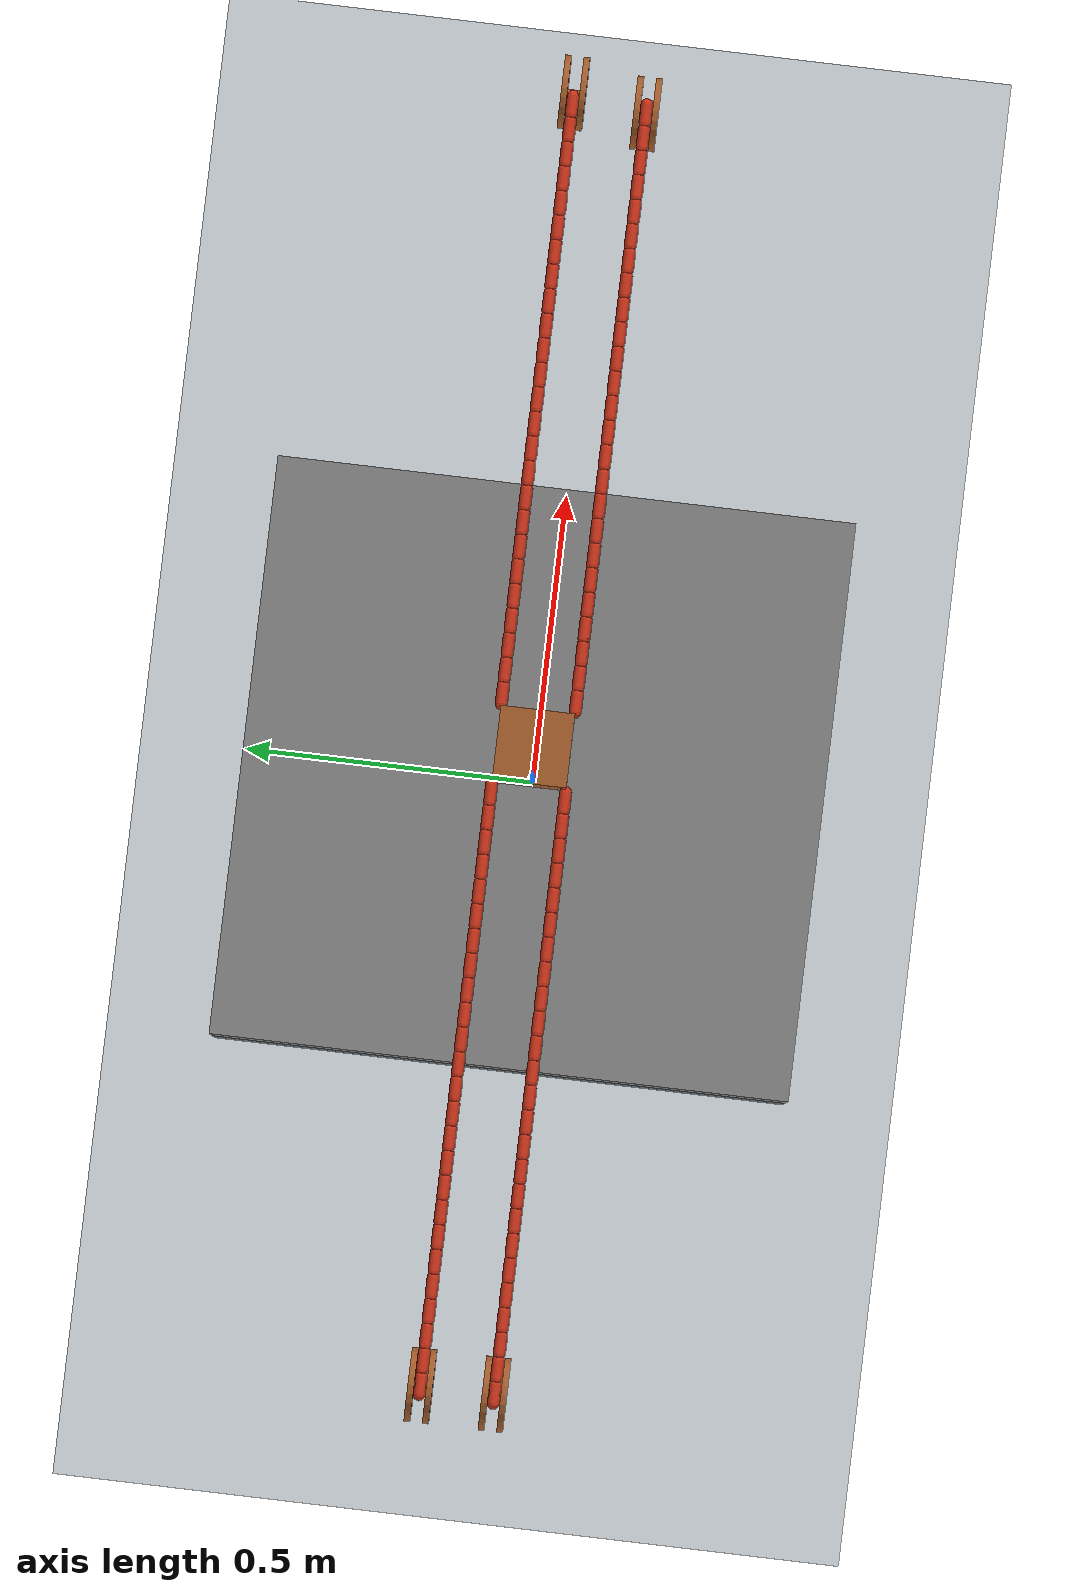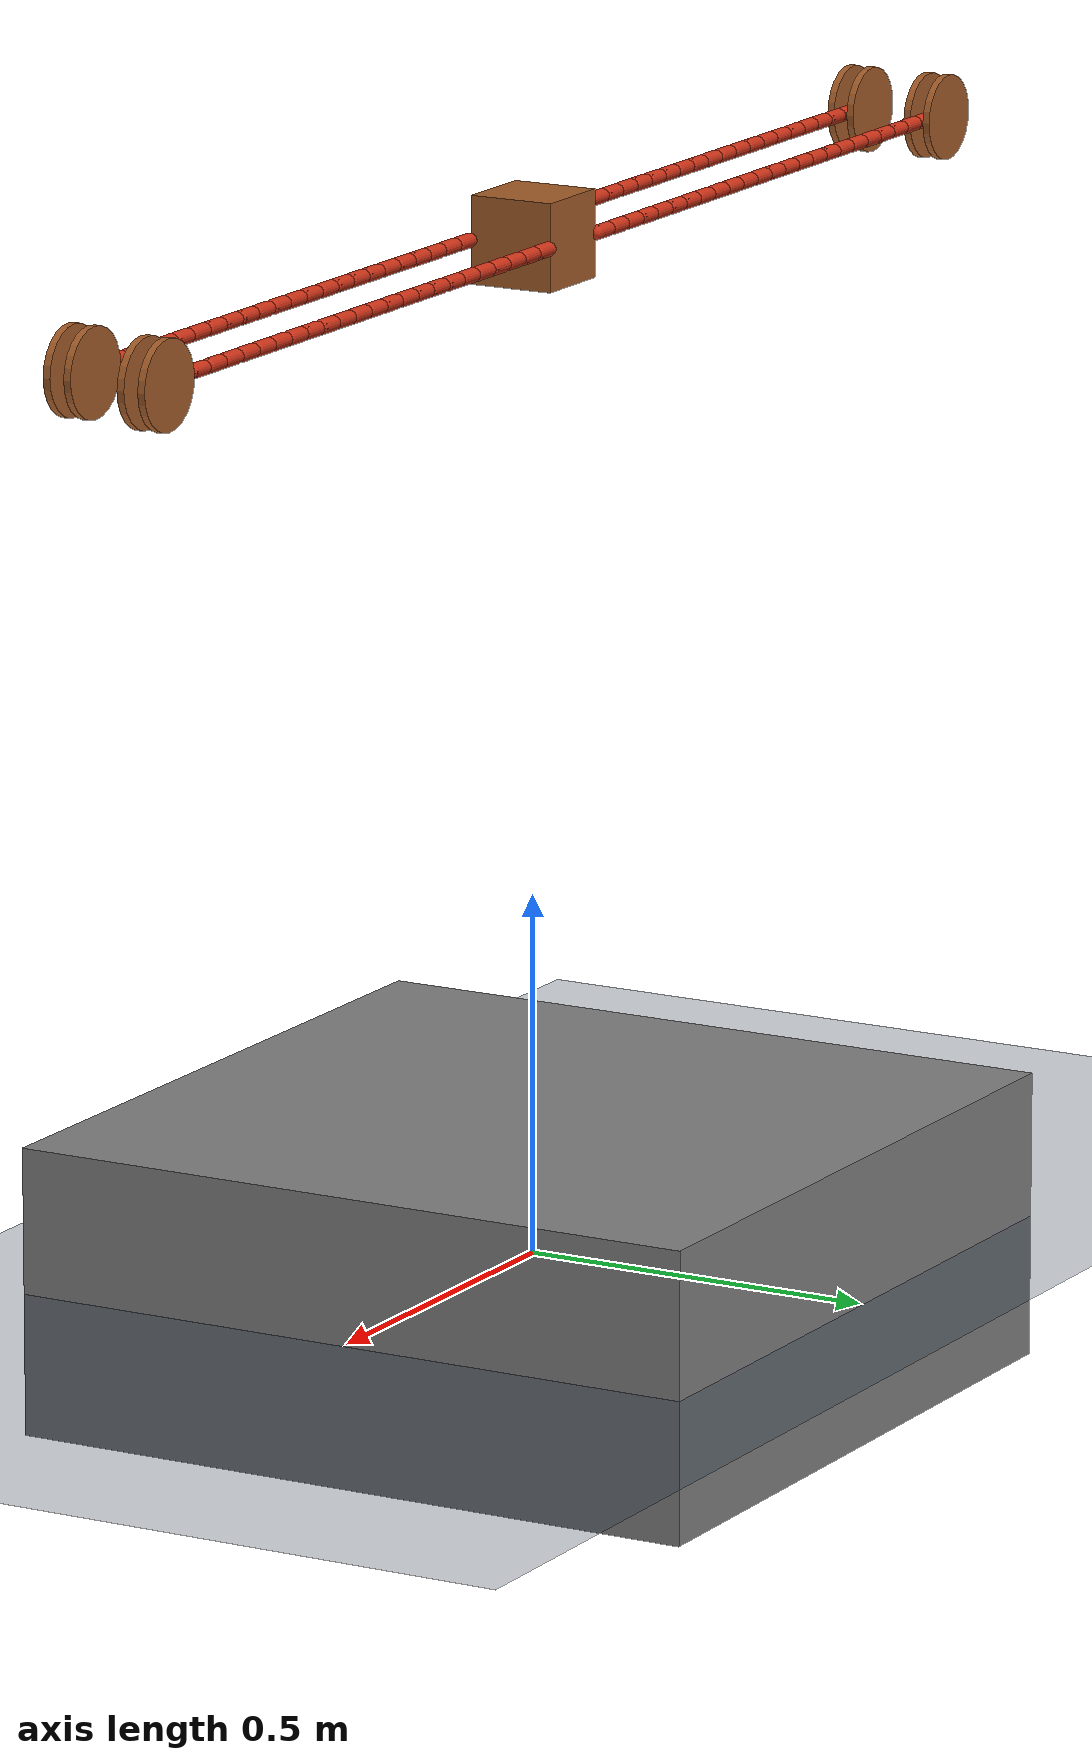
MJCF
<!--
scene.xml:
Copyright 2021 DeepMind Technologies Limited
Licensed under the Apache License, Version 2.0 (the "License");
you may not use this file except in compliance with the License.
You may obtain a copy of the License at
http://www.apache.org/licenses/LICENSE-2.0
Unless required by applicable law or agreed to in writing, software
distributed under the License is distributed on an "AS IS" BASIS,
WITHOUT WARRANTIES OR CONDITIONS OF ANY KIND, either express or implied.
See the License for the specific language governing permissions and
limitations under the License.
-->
<?xml version="1.0" encoding="UTF-8"?>

<mujoco model="d2w_cables">
  <include file="scene.xml"/>

  <option timestep="0.001" jacobian="dense"/>

  <size nconmax="300" njmax="1000" nstack="500000"/>

  <asset>
    <texture type="skybox" builtin="gradient" rgb1=".3 .5 .7" rgb2="0 0 0" width="512" height="512"/>
    <texture name="body" type="cube" builtin="flat" mark="cross" width="127" height="1278"
             rgb1="0.8 0.6 0.4" rgb2="0.8 0.6 0.4" markrgb="1 1 1" random="0.01"/>
    <material name="body" texture="body" texuniform="true" rgba="0.8 0.6 .4 1"/>
    <texture name="grid" type="2d" builtin="checker" width="512" height="512" rgb1=".1 .2 .3" rgb2=".2 .3 .4"/>
    <material name="grid" texture="grid" texrepeat="1 1" texuniform="true" reflectance=".2"/>
  </asset>

  <default>
    <motor ctrlrange="-1 1" ctrllimited="true"/>
    <default class="body">
      <geom type="capsule" condim="1" friction=".7" solimp=".9 .99 .003" solref=".015 1" material="body"/>
      <joint type="hinge" damping=".2" stiffness="1" armature=".01" limited="true" solimplimit="0 .99 .01"/>
      <default class="big_joint">
        <joint damping="5" stiffness="10"/>
        <default class="big_stiff_joint">
          <joint stiffness="20"/>
        </default>
      </default>
    </default>
  </default>

  <visual>
    <map force="0.1" zfar="30"/>
    <rgba haze="0.15 0.25 0.35 1"/>
    <quality shadowsize="4096"/>
    <global offwidth="800" offheight="800"/>
  </visual>

  <worldbody>

    <body name="b_winch_5">
      <geom type="box" pos="0 0 0" size="0.5 0.5 0.2"/>
    </body>

      <!-- Last code Full body -->
    <body name="torso" pos="0 0 1.4" childclass="body">
        <light name="top" pos="0 0 1" mode="trackcom"/>
        <camera name="back" pos="-3 0 1" xyaxes="0 -1 0 1 0 2" mode="trackcom"/>
        <camera name="side" pos="0 -3 1" xyaxes="1 0 0 0 1 2" mode="trackcom"/>
        <freejoint name="root"/>
        <geom name="box" type="box" mass="0.5" fromto="0 -.06 0 0 .06 0" size=".06"/>

        <body name="R0B0" pos="0.08 0.06 0" euler="0 0 0">
            <inertial pos="0 0 0" quat="0.707107 0 0.707107 0" mass="0.0125664" diaginertia="1.98968e-06 1.98968e-06 6.28319e-07" />
            <geom name="R0G0" size="0.01 0.015" quat="0.707107 0 0.707107 0" condim="3" friction="1 0.005 0.0001" solref="0.02 1" solimp="0.9 0.95 0.001 0.5 2" rgba="0.8 0.2 0.1 1" />
            <body name="R0B1" pos="0.04 0 0">
                <inertial pos="0 0 0" quat="0.707107 0 0.707107 0" mass="0.0125664" diaginertia="1.98968e-06 1.98968e-06 6.28319e-07" />
                <joint name="R0J0_1" pos="-0.02 0 0" axis="0 1 0" group="3" limited="false" solimplimit="0.9 0.95 0.001 0.5 2" stiffness="0" armature="0" damping="0.005" />
                <joint name="R0J1_1" pos="-0.02 0 0" axis="0 0 1" group="3" limited="false" solimplimit="0.9 0.95 0.001 0.5 2" stiffness="0" armature="0" damping="0.005" />
                <geom name="R0G1" size="0.01 0.015" quat="0.707107 0 0.707107 0" condim="3" friction="1 0.005 0.0001" solref="0.02 1" solimp="0.9 0.95 0.001 0.5 2" rgba="0.8 0.2 0.1 1" />
                <body name="R0B2" pos="0.04 0 0">
                    <inertial pos="0 0 0" quat="0.707107 0 0.707107 0" mass="0.0125664" diaginertia="1.98968e-06 1.98968e-06 6.28319e-07" />
                    <joint name="R0J0_2" pos="-0.02 0 0" axis="0 1 0" group="3" limited="false" solimplimit="0.9 0.95 0.001 0.5 2" stiffness="0" armature="0" damping="0.005" />
                    <joint name="R0J1_2" pos="-0.02 0 0" axis="0 0 1" group="3" limited="false" solimplimit="0.9 0.95 0.001 0.5 2" stiffness="0" armature="0" damping="0.005" />
                    <geom name="R0G2" size="0.01 0.015" quat="0.707107 0 0.707107 0" condim="3" friction="1 0.005 0.0001" solref="0.02 1" solimp="0.9 0.95 0.001 0.5 2" rgba="0.8 0.2 0.1 1" />
                    <body name="R0B3" pos="0.04 0 0">
                        <inertial pos="0 0 0" quat="0.707107 0 0.707107 0" mass="0.0125664" diaginertia="1.98968e-06 1.98968e-06 6.28319e-07" />
                        <joint name="R0J0_3" pos="-0.02 0 0" axis="0 1 0" group="3" limited="false" solimplimit="0.9 0.95 0.001 0.5 2" stiffness="0" armature="0" damping="0.005" />
                        <joint name="R0J1_3" pos="-0.02 0 0" axis="0 0 1" group="3" limited="false" solimplimit="0.9 0.95 0.001 0.5 2" stiffness="0" armature="0" damping="0.005" />
                        <geom name="R0G3" size="0.01 0.015" quat="0.707107 0 0.707107 0" condim="3" friction="1 0.005 0.0001" solref="0.02 1" solimp="0.9 0.95 0.001 0.5 2" rgba="0.8 0.2 0.1 1" />
                        <body name="R0B4" pos="0.04 0 0">
                            <inertial pos="0 0 0" quat="0.707107 0 0.707107 0" mass="0.0125664" diaginertia="1.98968e-06 1.98968e-06 6.28319e-07" />
                            <joint name="R0J0_4" pos="-0.02 0 0" axis="0 1 0" group="3" limited="false" solimplimit="0.9 0.95 0.001 0.5 2" stiffness="0" armature="0" damping="0.005" />
                            <joint name="R0J1_4" pos="-0.02 0 0" axis="0 0 1" group="3" limited="false" solimplimit="0.9 0.95 0.001 0.5 2" stiffness="0" armature="0" damping="0.005" />
                            <geom name="R0G4" size="0.01 0.015" quat="0.707107 0 0.707107 0" condim="3" friction="1 0.005 0.0001" solref="0.02 1" solimp="0.9 0.95 0.001 0.5 2" rgba="0.8 0.2 0.1 1" />
                            <body name="R0B5" pos="0.04 0 0">
                                <inertial pos="0 0 0" quat="0.707107 0 0.707107 0" mass="0.0125664" diaginertia="1.98968e-06 1.98968e-06 6.28319e-07" />
                                <joint name="R0J0_5" pos="-0.02 0 0" axis="0 1 0" group="3" limited="false" solimplimit="0.9 0.95 0.001 0.5 2" stiffness="0" armature="0" damping="0.005" />
                                <joint name="R0J1_5" pos="-0.02 0 0" axis="0 0 1" group="3" limited="false" solimplimit="0.9 0.95 0.001 0.5 2" stiffness="0" armature="0" damping="0.005" />
                                <geom name="R0G5" size="0.01 0.015" quat="0.707107 0 0.707107 0" condim="3" friction="1 0.005 0.0001" solref="0.02 1" solimp="0.9 0.95 0.001 0.5 2" rgba="0.8 0.2 0.1 1" />
                                <body name="R0B6" pos="0.04 0 0">
                                    <inertial pos="0 0 0" quat="0.707107 0 0.707107 0" mass="0.0125664" diaginertia="1.98968e-06 1.98968e-06 6.28319e-07" />
                                    <joint name="R0J0_6" pos="-0.02 0 0" axis="0 1 0" group="3" limited="false" solimplimit="0.9 0.95 0.001 0.5 2" stiffness="0" armature="0" damping="0.005" />
                                    <joint name="R0J1_6" pos="-0.02 0 0" axis="0 0 1" group="3" limited="false" solimplimit="0.9 0.95 0.001 0.5 2" stiffness="0" armature="0" damping="0.005" />
                                    <geom name="R0G6" size="0.01 0.015" quat="0.707107 0 0.707107 0" condim="3" friction="1 0.005 0.0001" solref="0.02 1" solimp="0.9 0.95 0.001 0.5 2" rgba="0.8 0.2 0.1 1" />
                                    <body name="R0B7" pos="0.04 0 0">
                                        <inertial pos="0 0 0" quat="0.707107 0 0.707107 0" mass="0.0125664" diaginertia="1.98968e-06 1.98968e-06 6.28319e-07" />
                                        <joint name="R0J0_7" pos="-0.02 0 0" axis="0 1 0" group="3" limited="false" solimplimit="0.9 0.95 0.001 0.5 2" stiffness="0" armature="0" damping="0.005" />
                                        <joint name="R0J1_7" pos="-0.02 0 0" axis="0 0 1" group="3" limited="false" solimplimit="0.9 0.95 0.001 0.5 2" stiffness="0" armature="0" damping="0.005" />
                                        <geom name="R0G7" size="0.01 0.015" quat="0.707107 0 0.707107 0" condim="3" friction="1 0.005 0.0001" solref="0.02 1" solimp="0.9 0.95 0.001 0.5 2" rgba="0.8 0.2 0.1 1" />
                                        <body name="R0B8" pos="0.04 0 0">
                                            <inertial pos="0 0 0" quat="0.707107 0 0.707107 0" mass="0.0125664" diaginertia="1.98968e-06 1.98968e-06 6.28319e-07" />
                                            <joint name="R0J0_8" pos="-0.02 0 0" axis="0 1 0" group="3" limited="false" solimplimit="0.9 0.95 0.001 0.5 2" stiffness="0" armature="0" damping="0.005" />
                                            <joint name="R0J1_8" pos="-0.02 0 0" axis="0 0 1" group="3" limited="false" solimplimit="0.9 0.95 0.001 0.5 2" stiffness="0" armature="0" damping="0.005" />
                                            <geom name="R0G8" size="0.01 0.015" quat="0.707107 0 0.707107 0" condim="3" friction="1 0.005 0.0001" solref="0.02 1" solimp="0.9 0.95 0.001 0.5 2" rgba="0.8 0.2 0.1 1" />
                                            <body name="R0B9" pos="0.04 0 0">
                                                <inertial pos="0 0 0" quat="0.707107 0 0.707107 0" mass="0.0125664" diaginertia="1.98968e-06 1.98968e-06 6.28319e-07" />
                                                <joint name="R0J0_9" pos="-0.02 0 0" axis="0 1 0" group="3" limited="false" solimplimit="0.9 0.95 0.001 0.5 2" stiffness="0" armature="0" damping="0.005" />
                                                <joint name="R0J1_9" pos="-0.02 0 0" axis="0 0 1" group="3" limited="false" solimplimit="0.9 0.95 0.001 0.5 2" stiffness="0" armature="0" damping="0.005" />
                                                <geom name="R0G9" size="0.01 0.015" quat="0.707107 0 0.707107 0" condim="3" friction="1 0.005 0.0001" solref="0.02 1" solimp="0.9 0.95 0.001 0.5 2" rgba="0.8 0.2 0.1 1" />
                                                <body name="R0B10" pos="0.04 0 0">
                                                    <inertial pos="0 0 0" quat="0.707107 0 0.707107 0" mass="0.0125664" diaginertia="1.98968e-06 1.98968e-06 6.28319e-07" />
                                                    <joint name="R0J0_10" pos="-0.02 0 0" axis="0 1 0" group="3" limited="false" solimplimit="0.9 0.95 0.001 0.5 2" stiffness="0" armature="0" damping="0.005" />
                                                    <joint name="R0J1_10" pos="-0.02 0 0" axis="0 0 1" group="3" limited="false" solimplimit="0.9 0.95 0.001 0.5 2" stiffness="0" armature="0" damping="0.005" />
                                                    <geom name="R0G10" size="0.01 0.015" quat="0.707107 0 0.707107 0" condim="3" friction="1 0.005 0.0001" solref="0.02 1" solimp="0.9 0.95 0.001 0.5 2" rgba="0.8 0.2 0.1 1" />
                                                    <body name="R0B11" pos="0.04 0 0">
                                                        <inertial pos="0 0 0" quat="0.707107 0 0.707107 0" mass="0.0125664" diaginertia="1.98968e-06 1.98968e-06 6.28319e-07" />
                                                        <joint name="R0J0_11" pos="-0.02 0 0" axis="0 1 0" group="3" limited="false" solimplimit="0.9 0.95 0.001 0.5 2" stiffness="0" armature="0" damping="0.005" />
                                                        <joint name="R0J1_11" pos="-0.02 0 0" axis="0 0 1" group="3" limited="false" solimplimit="0.9 0.95 0.001 0.5 2" stiffness="0" armature="0" damping="0.005" />
                                                        <geom name="R0G11" size="0.01 0.015" quat="0.707107 0 0.707107 0" condim="3" friction="1 0.005 0.0001" solref="0.02 1" solimp="0.9 0.95 0.001 0.5 2" rgba="0.8 0.2 0.1 1" />
                                                        <body name="R0B12" pos="0.04 0 0">
                                                            <inertial pos="0 0 0" quat="0.707107 0 0.707107 0" mass="0.0125664" diaginertia="1.98968e-06 1.98968e-06 6.28319e-07" />
                                                            <joint name="R0J0_12" pos="-0.02 0 0" axis="0 1 0" group="3" limited="false" solimplimit="0.9 0.95 0.001 0.5 2" stiffness="0" armature="0" damping="0.005" />
                                                            <joint name="R0J1_12" pos="-0.02 0 0" axis="0 0 1" group="3" limited="false" solimplimit="0.9 0.95 0.001 0.5 2" stiffness="0" armature="0" damping="0.005" />
                                                            <geom name="R0G12" size="0.01 0.015" quat="0.707107 0 0.707107 0" condim="3" friction="1 0.005 0.0001" solref="0.02 1" solimp="0.9 0.95 0.001 0.5 2" rgba="0.8 0.2 0.1 1" />
                                                            <body name="R0B13" pos="0.04 0 0">
                                                                <inertial pos="0 0 0" quat="0.707107 0 0.707107 0" mass="0.0125664" diaginertia="1.98968e-06 1.98968e-06 6.28319e-07" />
                                                                <joint name="R0J0_13" pos="-0.02 0 0" axis="0 1 0" group="3" limited="false" solimplimit="0.9 0.95 0.001 0.5 2" stiffness="0" armature="0" damping="0.005" />
                                                                <joint name="R0J1_13" pos="-0.02 0 0" axis="0 0 1" group="3" limited="false" solimplimit="0.9 0.95 0.001 0.5 2" stiffness="0" armature="0" damping="0.005" />
                                                                <geom name="R0G13" size="0.01 0.015" quat="0.707107 0 0.707107 0" condim="3" friction="1 0.005 0.0001" solref="0.02 1" solimp="0.9 0.95 0.001 0.5 2" rgba="0.8 0.2 0.1 1" />
                                                                <body name="R0B14" pos="0.04 0 0">
                                                                    <inertial pos="0 0 0" quat="0.707107 0 0.707107 0" mass="0.0125664" diaginertia="1.98968e-06 1.98968e-06 6.28319e-07" />
                                                                    <joint name="R0J0_14" pos="-0.02 0 0" axis="0 1 0" group="3" limited="false" solimplimit="0.9 0.95 0.001 0.5 2" stiffness="0" armature="0" damping="0.005" />
                                                                    <joint name="R0J1_14" pos="-0.02 0 0" axis="0 0 1" group="3" limited="false" solimplimit="0.9 0.95 0.001 0.5 2" stiffness="0" armature="0" damping="0.005" />
                                                                    <geom name="R0G14" size="0.01 0.015" quat="0.707107 0 0.707107 0" condim="3" friction="1 0.005 0.0001" solref="0.02 1" solimp="0.9 0.95 0.001 0.5 2" rgba="0.8 0.2 0.1 1" />
                                                                    <body name="R0B15" pos="0.04 0 0">
                                                                        <inertial pos="0 0 0" quat="0.707107 0 0.707107 0" mass="0.0125664" diaginertia="1.98968e-06 1.98968e-06 6.28319e-07" />
                                                                        <joint name="R0J0_15" pos="-0.02 0 0" axis="0 1 0" group="3" limited="false" solimplimit="0.9 0.95 0.001 0.5 2" stiffness="0" armature="0" damping="0.005" />
                                                                        <joint name="R0J1_15" pos="-0.02 0 0" axis="0 0 1" group="3" limited="false" solimplimit="0.9 0.95 0.001 0.5 2" stiffness="0" armature="0" damping="0.005" />
                                                                        <geom name="R0G15" size="0.01 0.015" quat="0.707107 0 0.707107 0" condim="3" friction="1 0.005 0.0001" solref="0.02 1" solimp="0.9 0.95 0.001 0.5 2" rgba="0.8 0.2 0.1 1" />
                                                                        <body name="R0B16" pos="0.04 0 0">
                                                                            <inertial pos="0 0 0" quat="0.707107 0 0.707107 0" mass="0.0125664" diaginertia="1.98968e-06 1.98968e-06 6.28319e-07" />
                                                                            <joint name="R0J0_16" pos="-0.02 0 0" axis="0 1 0" group="3" limited="false" solimplimit="0.9 0.95 0.001 0.5 2" stiffness="0" armature="0" damping="0.005" />
                                                                            <joint name="R0J1_16" pos="-0.02 0 0" axis="0 0 1" group="3" limited="false" solimplimit="0.9 0.95 0.001 0.5 2" stiffness="0" armature="0" damping="0.005" />
                                                                            <geom name="R0G16" size="0.01 0.015" quat="0.707107 0 0.707107 0" condim="3" friction="1 0.005 0.0001" solref="0.02 1" solimp="0.9 0.95 0.001 0.5 2" rgba="0.8 0.2 0.1 1" />
                                                                            <body name="R0B17" pos="0.04 0 0">
                                                                                <inertial pos="0 0 0" quat="0.707107 0 0.707107 0" mass="0.0125664" diaginertia="1.98968e-06 1.98968e-06 6.28319e-07" />
                                                                                <joint name="R0J0_17" pos="-0.02 0 0" axis="0 1 0" group="3" limited="false" solimplimit="0.9 0.95 0.001 0.5 2" stiffness="0" armature="0" damping="0.005" />
                                                                                <joint name="R0J1_17" pos="-0.02 0 0" axis="0 0 1" group="3" limited="false" solimplimit="0.9 0.95 0.001 0.5 2" stiffness="0" armature="0" damping="0.005" />
                                                                                <geom name="R0G17" size="0.01 0.015" quat="0.707107 0 0.707107 0" condim="3" friction="1 0.005 0.0001" solref="0.02 1" solimp="0.9 0.95 0.001 0.5 2" rgba="0.8 0.2 0.1 1" />
                                                                                <body name="R0B18" pos="0.04 0 0">
                                                                                    <inertial pos="0 0 0" quat="0.707107 0 0.707107 0" mass="0.0125664" diaginertia="1.98968e-06 1.98968e-06 6.28319e-07" />
                                                                                    <joint name="R0J0_18" pos="-0.02 0 0" axis="0 1 0" group="3" limited="false" solimplimit="0.9 0.95 0.001 0.5 2" stiffness="0" armature="0" damping="0.005" />
                                                                                    <joint name="R0J1_18" pos="-0.02 0 0" axis="0 0 1" group="3" limited="false" solimplimit="0.9 0.95 0.001 0.5 2" stiffness="0" armature="0" damping="0.005" />
                                                                                    <geom name="R0G18" size="0.01 0.015" quat="0.707107 0 0.707107 0" condim="3" friction="1 0.005 0.0001" solref="0.02 1" solimp="0.9 0.95 0.001 0.5 2" rgba="0.8 0.2 0.1 1" />
                                                                                    <body name="R0B19" pos="0.04 0 0">
                                                                                        <inertial pos="0 0 0" quat="0.707107 0 0.707107 0" mass="0.0125664" diaginertia="1.98968e-06 1.98968e-06 6.28319e-07" />
                                                                                        <joint name="R0J0_19" pos="-0.02 0 0" axis="0 1 0" group="3" limited="false" solimplimit="0.9 0.95 0.001 0.5 2" stiffness="0" armature="0" damping="0.005" />
                                                                                        <joint name="R0J1_19" pos="-0.02 0 0" axis="0 0 1" group="3" limited="false" solimplimit="0.9 0.95 0.001 0.5 2" stiffness="0" armature="0" damping="0.005" />
                                                                                        <geom name="R0G19" size="0.01 0.015" quat="0.707107 0 0.707107 0" condim="3" friction="1 0.005 0.0001" solref="0.02 1" solimp="0.9 0.95 0.001 0.5 2" rgba="0.8 0.2 0.1 1" />
                                                                                        <body name="R0B20" pos="0.04 0 0">
                                                                                            <inertial pos="0 0 0" quat="0.707107 0 0.707107 0" mass="0.0125664" diaginertia="1.98968e-06 1.98968e-06 6.28319e-07" />
                                                                                            <joint name="R0J0_20" pos="-0.02 0 0" axis="0 1 0" group="3" limited="false" solimplimit="0.9 0.95 0.001 0.5 2" stiffness="0" armature="0" damping="0.005" />
                                                                                            <joint name="R0J1_20" pos="-0.02 0 0" axis="0 0 1" group="3" limited="false" solimplimit="0.9 0.95 0.001 0.5 2" stiffness="0" armature="0" damping="0.005" />
                                                                                            <geom name="R0G20" size="0.01 0.015" quat="0.707107 0 0.707107 0" condim="3" friction="1 0.005 0.0001" solref="0.02 1" solimp="0.9 0.95 0.001 0.5 2" rgba="0.8 0.2 0.1 1" />
                                                                                            <body name="R0B21" pos="0.04 0 0">
                                                                                                <inertial pos="0 0 0" quat="0.707107 0 0.707107 0" mass="0.0125664" diaginertia="1.98968e-06 1.98968e-06 6.28319e-07" />
                                                                                                <joint name="R0J0_21" pos="-0.02 0 0" axis="0 1 0" group="3" limited="false" solimplimit="0.9 0.95 0.001 0.5 2" stiffness="0" armature="0" damping="0.005" />
                                                                                                <joint name="R0J1_21" pos="-0.02 0 0" axis="0 0 1" group="3" limited="false" solimplimit="0.9 0.95 0.001 0.5 2" stiffness="0" armature="0" damping="0.005" />
                                                                                                <geom name="R0G21" size="0.01 0.015" quat="0.707107 0 0.707107 0" condim="3" friction="1 0.005 0.0001" solref="0.02 1" solimp="0.9 0.95 0.001 0.5 2" rgba="0.8 0.2 0.1 1" />
                                                                                                <body name="R0B22" pos="0.04 0 0">
                                                                                                    <inertial pos="0 0 0" quat="0.707107 0 0.707107 0" mass="0.0125664" diaginertia="1.98968e-06 1.98968e-06 6.28319e-07" />
                                                                                                    <joint name="R0J0_22" pos="-0.02 0 0" axis="0 1 0" group="3" limited="false" solimplimit="0.9 0.95 0.001 0.5 2" stiffness="0" armature="0" damping="0.005" />
                                                                                                    <joint name="R0J1_22" pos="-0.02 0 0" axis="0 0 1" group="3" limited="false" solimplimit="0.9 0.95 0.001 0.5 2" stiffness="0" armature="0" damping="0.005" />
                                                                                                    <geom name="R0G22" size="0.01 0.015" quat="0.707107 0 0.707107 0" condim="3" friction="1 0.005 0.0001" solref="0.02 1" solimp="0.9 0.95 0.001 0.5 2" rgba="0.8 0.2 0.1 1" />
                                                                                                    <body name="R0B23" pos="0.04 0 0">
                                                                                                        <inertial pos="0 0 0" quat="0.707107 0 0.707107 0" mass="0.0125664" diaginertia="1.98968e-06 1.98968e-06 6.28319e-07" />
                                                                                                        <joint name="R0J0_23" pos="-0.02 0 0" axis="0 1 0" group="3" limited="false" solimplimit="0.9 0.95 0.001 0.5 2" stiffness="0" armature="0" damping="0.005" />
                                                                                                        <joint name="R0J1_23" pos="-0.02 0 0" axis="0 0 1" group="3" limited="false" solimplimit="0.9 0.95 0.001 0.5 2" stiffness="0" armature="0" damping="0.005" />
                                                                                                        <geom name="R0G23" size="0.01 0.015" quat="0.707107 0 0.707107 0" condim="3" friction="1 0.005 0.0001" solref="0.02 1" solimp="0.9 0.95 0.001 0.5 2" rgba="0.8 0.2 0.1 1" />
                                                                                                        <body name="R0B24" pos="0.04 0 0">
                                                                                                            <inertial pos="0 0 0" quat="0.707107 0 0.707107 0" mass="0.0125664" diaginertia="1.98968e-06 1.98968e-06 6.28319e-07" />
                                                                                                            <joint name="R0J0_24" pos="-0.02 0 0" axis="0 1 0" group="3" limited="false" solimplimit="0.9 0.95 0.001 0.5 2" stiffness="0" armature="0" damping="0.005" />
                                                                                                            <joint name="R0J1_24" pos="-0.02 0 0" axis="0 0 1" group="3" limited="false" solimplimit="0.9 0.95 0.001 0.5 2" stiffness="0" armature="0" damping="0.005" />
                                                                                                            <geom name="R0G24" size="0.01 0.015" quat="0.707107 0 0.707107 0" condim="3" friction="1 0.005 0.0001" solref="0.02 1" solimp="0.9 0.95 0.001 0.5 2" rgba="0.8 0.2 0.1 1" />
                                                                                                            <body name="b_winch_0" euler="90 0 0" pos="0.02 0 0">
                                                                                                                <joint type="hinge" axis="0 0 1" name="winch_0" range="-1.5708 1.5708"/>
                                                                                                                <geom type="cylinder" solimp=".9 .99 .003" priority="2" condim="6" fromto="0 0 -0.01 0 0 0.02" size="0.005"/>
                                                                                                                <geom type="cylinder" euler= "90 90 0" priority="2" condim="6" fromto="0 0 -0.01 0 0 -0.02" size="0.06"/>
                                                                                                                <geom type="cylinder" euler= "90 90 0" priority="2" condim="6" fromto="0 0 0.01 0 0 0.02" size="0.06"/>
                                                                                                            </body>
                                                                                                        </body>
                                                                                                    </body>
                                                                                                </body>
                                                                                            </body>
                                                                                        </body>
                                                                                    </body>
                                                                                </body>
                                                                            </body>
                                                                        </body>
                                                                    </body>
                                                                </body>
                                                            </body>
                                                        </body>
                                                    </body>
                                                </body>
                                            </body>
                                        </body>
                                    </body>
                                </body>
                            </body>
                        </body>
                    </body>
                </body>
            </body>
        </body>

        <body name="R1B0"  pos="-0.08 0.06 0" euler="0 180 0">
            <inertial pos="0 0 0" quat="0.707107 0 0.707107 0" mass="0.0125664" diaginertia="1.98968e-06 1.98968e-06 6.28319e-07" />
            <joint name="R1J0_0" pos="0.02 0 0" axis="0 1 0" group="3" limited="false" solimplimit="0.9 0.95 0.001 0.5 2" stiffness="0" armature="0" damping="0.005" />
            <joint name="R1J1_0" pos="0.02 0 0" axis="0 0 1" group="3" limited="false" solimplimit="0.9 0.95 0.001 0.5 2" stiffness="0" armature="0" damping="0.005" />
            <geom name="R1G0" size="0.01 0.015" quat="0.707107 0 0.707107 0" condim="3" friction="1 0.005 0.0001" solref="0.02 1" solimp="0.9 0.95 0.001 0.5 2" rgba="0.8 0.2 0.1 1" />
            <body name="R1B1" pos="0.04 0 0">
                <inertial pos="0 0 0" quat="0.707107 0 0.707107 0" mass="0.0125664" diaginertia="1.98968e-06 1.98968e-06 6.28319e-07" />
                <geom name="R1G1" size="0.01 0.015" quat="0.707107 0 0.707107 0" condim="3" friction="1 0.005 0.0001" solref="0.02 1" solimp="0.9 0.95 0.001 0.5 2" rgba="0.8 0.2 0.1 1" />
                <body name="R1B2" pos="0.04 0 0">
                    <inertial pos="0 0 0" quat="0.707107 0 0.707107 0" mass="0.0125664" diaginertia="1.98968e-06 1.98968e-06 6.28319e-07" />
                    <joint name="R1J0_2" pos="-0.02 0 0" axis="0 1 0" group="3" limited="false" solimplimit="0.9 0.95 0.001 0.5 2" stiffness="0" armature="0" damping="0.005" />
                    <joint name="R1J1_2" pos="-0.02 0 0" axis="0 0 1" group="3" limited="false" solimplimit="0.9 0.95 0.001 0.5 2" stiffness="0" armature="0" damping="0.005" />
                    <geom name="R1G2" size="0.01 0.015" quat="0.707107 0 0.707107 0" condim="3" friction="1 0.005 0.0001" solref="0.02 1" solimp="0.9 0.95 0.001 0.5 2" rgba="0.8 0.2 0.1 1" />
                    <body name="R1B3" pos="0.04 0 0">
                        <inertial pos="0 0 0" quat="0.707107 0 0.707107 0" mass="0.0125664" diaginertia="1.98968e-06 1.98968e-06 6.28319e-07" />
                        <joint name="R1J0_3" pos="-0.02 0 0" axis="0 1 0" group="3" limited="false" solimplimit="0.9 0.95 0.001 0.5 2" stiffness="0" armature="0" damping="0.005" />
                        <joint name="R1J1_3" pos="-0.02 0 0" axis="0 0 1" group="3" limited="false" solimplimit="0.9 0.95 0.001 0.5 2" stiffness="0" armature="0" damping="0.005" />
                        <geom name="R1G3" size="0.01 0.015" quat="0.707107 0 0.707107 0" condim="3" friction="1 0.005 0.0001" solref="0.02 1" solimp="0.9 0.95 0.001 0.5 2" rgba="0.8 0.2 0.1 1" />
                        <body name="R1B4" pos="0.04 0 0">
                            <inertial pos="0 0 0" quat="0.707107 0 0.707107 0" mass="0.0125664" diaginertia="1.98968e-06 1.98968e-06 6.28319e-07" />
                            <joint name="R1J0_4" pos="-0.02 0 0" axis="0 1 0" group="3" limited="false" solimplimit="0.9 0.95 0.001 0.5 2" stiffness="0" armature="0" damping="0.005" />
                            <joint name="R1J1_4" pos="-0.02 0 0" axis="0 0 1" group="3" limited="false" solimplimit="0.9 0.95 0.001 0.5 2" stiffness="0" armature="0" damping="0.005" />
                            <geom name="R1G4" size="0.01 0.015" quat="0.707107 0 0.707107 0" condim="3" friction="1 0.005 0.0001" solref="0.02 1" solimp="0.9 0.95 0.001 0.5 2" rgba="0.8 0.2 0.1 1" />
                            <body name="R1B5" pos="0.04 0 0">
                                <inertial pos="0 0 0" quat="0.707107 0 0.707107 0" mass="0.0125664" diaginertia="1.98968e-06 1.98968e-06 6.28319e-07" />
                                <joint name="R1J0_5" pos="-0.02 0 0" axis="0 1 0" group="3" limited="false" solimplimit="0.9 0.95 0.001 0.5 2" stiffness="0" armature="0" damping="0.005" />
                                <joint name="R1J1_5" pos="-0.02 0 0" axis="0 0 1" group="3" limited="false" solimplimit="0.9 0.95 0.001 0.5 2" stiffness="0" armature="0" damping="0.005" />
                                <geom name="R1G5" size="0.01 0.015" quat="0.707107 0 0.707107 0" condim="3" friction="1 0.005 0.0001" solref="0.02 1" solimp="0.9 0.95 0.001 0.5 2" rgba="0.8 0.2 0.1 1" />
                                <body name="R1B6" pos="0.04 0 0">
                                    <inertial pos="0 0 0" quat="0.707107 0 0.707107 0" mass="0.0125664" diaginertia="1.98968e-06 1.98968e-06 6.28319e-07" />
                                    <joint name="R1J0_6" pos="-0.02 0 0" axis="0 1 0" group="3" limited="false" solimplimit="0.9 0.95 0.001 0.5 2" stiffness="0" armature="0" damping="0.005" />
                                    <joint name="R1J1_6" pos="-0.02 0 0" axis="0 0 1" group="3" limited="false" solimplimit="0.9 0.95 0.001 0.5 2" stiffness="0" armature="0" damping="0.005" />
                                    <geom name="R1G6" size="0.01 0.015" quat="0.707107 0 0.707107 0" condim="3" friction="1 0.005 0.0001" solref="0.02 1" solimp="0.9 0.95 0.001 0.5 2" rgba="0.8 0.2 0.1 1" />
                                    <body name="R1B7" pos="0.04 0 0">
                                        <inertial pos="0 0 0" quat="0.707107 0 0.707107 0" mass="0.0125664" diaginertia="1.98968e-06 1.98968e-06 6.28319e-07" />
                                        <joint name="R1J0_7" pos="-0.02 0 0" axis="0 1 0" group="3" limited="false" solimplimit="0.9 0.95 0.001 0.5 2" stiffness="0" armature="0" damping="0.005" />
                                        <joint name="R1J1_7" pos="-0.02 0 0" axis="0 0 1" group="3" limited="false" solimplimit="0.9 0.95 0.001 0.5 2" stiffness="0" armature="0" damping="0.005" />
                                        <geom name="R1G7" size="0.01 0.015" quat="0.707107 0 0.707107 0" condim="3" friction="1 0.005 0.0001" solref="0.02 1" solimp="0.9 0.95 0.001 0.5 2" rgba="0.8 0.2 0.1 1" />
                                        <body name="R1B8" pos="0.04 0 0">
                                            <inertial pos="0 0 0" quat="0.707107 0 0.707107 0" mass="0.0125664" diaginertia="1.98968e-06 1.98968e-06 6.28319e-07" />
                                            <joint name="R1J0_8" pos="-0.02 0 0" axis="0 1 0" group="3" limited="false" solimplimit="0.9 0.95 0.001 0.5 2" stiffness="0" armature="0" damping="0.005" />
                                            <joint name="R1J1_8" pos="-0.02 0 0" axis="0 0 1" group="3" limited="false" solimplimit="0.9 0.95 0.001 0.5 2" stiffness="0" armature="0" damping="0.005" />
                                            <geom name="R1G8" size="0.01 0.015" quat="0.707107 0 0.707107 0" condim="3" friction="1 0.005 0.0001" solref="0.02 1" solimp="0.9 0.95 0.001 0.5 2" rgba="0.8 0.2 0.1 1" />
                                            <body name="R1B9" pos="0.04 0 0">
                                                <inertial pos="0 0 0" quat="0.707107 0 0.707107 0" mass="0.0125664" diaginertia="1.98968e-06 1.98968e-06 6.28319e-07" />
                                                <joint name="R1J0_9" pos="-0.02 0 0" axis="0 1 0" group="3" limited="false" solimplimit="0.9 0.95 0.001 0.5 2" stiffness="0" armature="0" damping="0.005" />
                                                <joint name="R1J1_9" pos="-0.02 0 0" axis="0 0 1" group="3" limited="false" solimplimit="0.9 0.95 0.001 0.5 2" stiffness="0" armature="0" damping="0.005" />
                                                <geom name="R1G9" size="0.01 0.015" quat="0.707107 0 0.707107 0" condim="3" friction="1 0.005 0.0001" solref="0.02 1" solimp="0.9 0.95 0.001 0.5 2" rgba="0.8 0.2 0.1 1" />
                                                <body name="R1B10" pos="0.04 0 0">
                                                    <inertial pos="0 0 0" quat="0.707107 0 0.707107 0" mass="0.0125664" diaginertia="1.98968e-06 1.98968e-06 6.28319e-07" />
                                                    <joint name="R1J0_10" pos="-0.02 0 0" axis="0 1 0" group="3" limited="false" solimplimit="0.9 0.95 0.001 0.5 2" stiffness="0" armature="0" damping="0.005" />
                                                    <joint name="R1J1_10" pos="-0.02 0 0" axis="0 0 1" group="3" limited="false" solimplimit="0.9 0.95 0.001 0.5 2" stiffness="0" armature="0" damping="0.005" />
                                                    <geom name="R1G10" size="0.01 0.015" quat="0.707107 0 0.707107 0" condim="3" friction="1 0.005 0.0001" solref="0.02 1" solimp="0.9 0.95 0.001 0.5 2" rgba="0.8 0.2 0.1 1" />
                                                    <body name="R1B11" pos="0.04 0 0">
                                                        <inertial pos="0 0 0" quat="0.707107 0 0.707107 0" mass="0.0125664" diaginertia="1.98968e-06 1.98968e-06 6.28319e-07" />
                                                        <joint name="R1J0_11" pos="-0.02 0 0" axis="0 1 0" group="3" limited="false" solimplimit="0.9 0.95 0.001 0.5 2" stiffness="0" armature="0" damping="0.005" />
                                                        <joint name="R1J1_11" pos="-0.02 0 0" axis="0 0 1" group="3" limited="false" solimplimit="0.9 0.95 0.001 0.5 2" stiffness="0" armature="0" damping="0.005" />
                                                        <geom name="R1G11" size="0.01 0.015" quat="0.707107 0 0.707107 0" condim="3" friction="1 0.005 0.0001" solref="0.02 1" solimp="0.9 0.95 0.001 0.5 2" rgba="0.8 0.2 0.1 1" />
                                                        <body name="R1B12" pos="0.04 0 0">
                                                            <inertial pos="0 0 0" quat="0.707107 0 0.707107 0" mass="0.0125664" diaginertia="1.98968e-06 1.98968e-06 6.28319e-07" />
                                                            <joint name="R1J0_12" pos="-0.02 0 0" axis="0 1 0" group="3" limited="false" solimplimit="0.9 0.95 0.001 0.5 2" stiffness="0" armature="0" damping="0.005" />
                                                            <joint name="R1J1_12" pos="-0.02 0 0" axis="0 0 1" group="3" limited="false" solimplimit="0.9 0.95 0.001 0.5 2" stiffness="0" armature="0" damping="0.005" />
                                                            <geom name="R1G12" size="0.01 0.015" quat="0.707107 0 0.707107 0" condim="3" friction="1 0.005 0.0001" solref="0.02 1" solimp="0.9 0.95 0.001 0.5 2" rgba="0.8 0.2 0.1 1" />
                                                            <body name="R1B13" pos="0.04 0 0">
                                                                <inertial pos="0 0 0" quat="0.707107 0 0.707107 0" mass="0.0125664" diaginertia="1.98968e-06 1.98968e-06 6.28319e-07" />
                                                                <joint name="R1J0_13" pos="-0.02 0 0" axis="0 1 0" group="3" limited="false" solimplimit="0.9 0.95 0.001 0.5 2" stiffness="0" armature="0" damping="0.005" />
                                                                <joint name="R1J1_13" pos="-0.02 0 0" axis="0 0 1" group="3" limited="false" solimplimit="0.9 0.95 0.001 0.5 2" stiffness="0" armature="0" damping="0.005" />
                                                                <geom name="R1G13" size="0.01 0.015" quat="0.707107 0 0.707107 0" condim="3" friction="1 0.005 0.0001" solref="0.02 1" solimp="0.9 0.95 0.001 0.5 2" rgba="0.8 0.2 0.1 1" />
                                                                <body name="R1B14" pos="0.04 0 0">
                                                                    <inertial pos="0 0 0" quat="0.707107 0 0.707107 0" mass="0.0125664" diaginertia="1.98968e-06 1.98968e-06 6.28319e-07" />
                                                                    <joint name="R1J0_14" pos="-0.02 0 0" axis="0 1 0" group="3" limited="false" solimplimit="0.9 0.95 0.001 0.5 2" stiffness="0" armature="0" damping="0.005" />
                                                                    <joint name="R1J1_14" pos="-0.02 0 0" axis="0 0 1" group="3" limited="false" solimplimit="0.9 0.95 0.001 0.5 2" stiffness="0" armature="0" damping="0.005" />
                                                                    <geom name="R1G14" size="0.01 0.015" quat="0.707107 0 0.707107 0" condim="3" friction="1 0.005 0.0001" solref="0.02 1" solimp="0.9 0.95 0.001 0.5 2" rgba="0.8 0.2 0.1 1" />
                                                                    <body name="R1B15" pos="0.04 0 0">
                                                                        <inertial pos="0 0 0" quat="0.707107 0 0.707107 0" mass="0.0125664" diaginertia="1.98968e-06 1.98968e-06 6.28319e-07" />
                                                                        <joint name="R1J0_15" pos="-0.02 0 0" axis="0 1 0" group="3" limited="false" solimplimit="0.9 0.95 0.001 0.5 2" stiffness="0" armature="0" damping="0.005" />
                                                                        <joint name="R1J1_15" pos="-0.02 0 0" axis="0 0 1" group="3" limited="false" solimplimit="0.9 0.95 0.001 0.5 2" stiffness="0" armature="0" damping="0.005" />
                                                                        <geom name="R1G15" size="0.01 0.015" quat="0.707107 0 0.707107 0" condim="3" friction="1 0.005 0.0001" solref="0.02 1" solimp="0.9 0.95 0.001 0.5 2" rgba="0.8 0.2 0.1 1" />
                                                                        <body name="R1B16" pos="0.04 0 0">
                                                                            <inertial pos="0 0 0" quat="0.707107 0 0.707107 0" mass="0.0125664" diaginertia="1.98968e-06 1.98968e-06 6.28319e-07" />
                                                                            <joint name="R1J0_16" pos="-0.02 0 0" axis="0 1 0" group="3" limited="false" solimplimit="0.9 0.95 0.001 0.5 2" stiffness="0" armature="0" damping="0.005" />
                                                                            <joint name="R1J1_16" pos="-0.02 0 0" axis="0 0 1" group="3" limited="false" solimplimit="0.9 0.95 0.001 0.5 2" stiffness="0" armature="0" damping="0.005" />
                                                                            <geom name="R1G16" size="0.01 0.015" quat="0.707107 0 0.707107 0" condim="3" friction="1 0.005 0.0001" solref="0.02 1" solimp="0.9 0.95 0.001 0.5 2" rgba="0.8 0.2 0.1 1" />
                                                                            <body name="R1B17" pos="0.04 0 0">
                                                                                <inertial pos="0 0 0" quat="0.707107 0 0.707107 0" mass="0.0125664" diaginertia="1.98968e-06 1.98968e-06 6.28319e-07" />
                                                                                <joint name="R1J0_17" pos="-0.02 0 0" axis="0 1 0" group="3" limited="false" solimplimit="0.9 0.95 0.001 0.5 2" stiffness="0" armature="0" damping="0.005" />
                                                                                <joint name="R1J1_17" pos="-0.02 0 0" axis="0 0 1" group="3" limited="false" solimplimit="0.9 0.95 0.001 0.5 2" stiffness="0" armature="0" damping="0.005" />
                                                                                <geom name="R1G17" size="0.01 0.015" quat="0.707107 0 0.707107 0" condim="3" friction="1 0.005 0.0001" solref="0.02 1" solimp="0.9 0.95 0.001 0.5 2" rgba="0.8 0.2 0.1 1" />
                                                                                <body name="R1B18" pos="0.04 0 0">
                                                                                    <inertial pos="0 0 0" quat="0.707107 0 0.707107 0" mass="0.0125664" diaginertia="1.98968e-06 1.98968e-06 6.28319e-07" />
                                                                                    <joint name="R1J0_18" pos="-0.02 0 0" axis="0 1 0" group="3" limited="false" solimplimit="0.9 0.95 0.001 0.5 2" stiffness="0" armature="0" damping="0.005" />
                                                                                    <joint name="R1J1_18" pos="-0.02 0 0" axis="0 0 1" group="3" limited="false" solimplimit="0.9 0.95 0.001 0.5 2" stiffness="0" armature="0" damping="0.005" />
                                                                                    <geom name="R1G18" size="0.01 0.015" quat="0.707107 0 0.707107 0" condim="3" friction="1 0.005 0.0001" solref="0.02 1" solimp="0.9 0.95 0.001 0.5 2" rgba="0.8 0.2 0.1 1" />
                                                                                    <body name="R1B19" pos="0.04 0 0">
                                                                                        <inertial pos="0 0 0" quat="0.707107 0 0.707107 0" mass="0.0125664" diaginertia="1.98968e-06 1.98968e-06 6.28319e-07" />
                                                                                        <joint name="R1J0_19" pos="-0.02 0 0" axis="0 1 0" group="3" limited="false" solimplimit="0.9 0.95 0.001 0.5 2" stiffness="0" armature="0" damping="0.005" />
                                                                                        <joint name="R1J1_19" pos="-0.02 0 0" axis="0 0 1" group="3" limited="false" solimplimit="0.9 0.95 0.001 0.5 2" stiffness="0" armature="0" damping="0.005" />
                                                                                        <geom name="R1G19" size="0.01 0.015" quat="0.707107 0 0.707107 0" condim="3" friction="1 0.005 0.0001" solref="0.02 1" solimp="0.9 0.95 0.001 0.5 2" rgba="0.8 0.2 0.1 1" />
                                                                                        <body name="R1B20" pos="0.04 0 0">
                                                                                            <inertial pos="0 0 0" quat="0.707107 0 0.707107 0" mass="0.0125664" diaginertia="1.98968e-06 1.98968e-06 6.28319e-07" />
                                                                                            <joint name="R1J0_20" pos="-0.02 0 0" axis="0 1 0" group="3" limited="false" solimplimit="0.9 0.95 0.001 0.5 2" stiffness="0" armature="0" damping="0.005" />
                                                                                            <joint name="R1J1_20" pos="-0.02 0 0" axis="0 0 1" group="3" limited="false" solimplimit="0.9 0.95 0.001 0.5 2" stiffness="0" armature="0" damping="0.005" />
                                                                                            <geom name="R1G20" size="0.01 0.015" quat="0.707107 0 0.707107 0" condim="3" friction="1 0.005 0.0001" solref="0.02 1" solimp="0.9 0.95 0.001 0.5 2" rgba="0.8 0.2 0.1 1" />
                                                                                            <body name="R1B21" pos="0.04 0 0">
                                                                                                <inertial pos="0 0 0" quat="0.707107 0 0.707107 0" mass="0.0125664" diaginertia="1.98968e-06 1.98968e-06 6.28319e-07" />
                                                                                                <joint name="R1J0_21" pos="-0.02 0 0" axis="0 1 0" group="3" limited="false" solimplimit="0.9 0.95 0.001 0.5 2" stiffness="0" armature="0" damping="0.005" />
                                                                                                <joint name="R1J1_21" pos="-0.02 0 0" axis="0 0 1" group="3" limited="false" solimplimit="0.9 0.95 0.001 0.5 2" stiffness="0" armature="0" damping="0.005" />
                                                                                                <geom name="R1G21" size="0.01 0.015" quat="0.707107 0 0.707107 0" condim="3" friction="1 0.005 0.0001" solref="0.02 1" solimp="0.9 0.95 0.001 0.5 2" rgba="0.8 0.2 0.1 1" />
                                                                                                <body name="R1B22" pos="0.04 0 0">
                                                                                                    <inertial pos="0 0 0" quat="0.707107 0 0.707107 0" mass="0.0125664" diaginertia="1.98968e-06 1.98968e-06 6.28319e-07" />
                                                                                                    <joint name="R1J0_22" pos="-0.02 0 0" axis="0 1 0" group="3" limited="false" solimplimit="0.9 0.95 0.001 0.5 2" stiffness="0" armature="0" damping="0.005" />
                                                                                                    <joint name="R1J1_22" pos="-0.02 0 0" axis="0 0 1" group="3" limited="false" solimplimit="0.9 0.95 0.001 0.5 2" stiffness="0" armature="0" damping="0.005" />
                                                                                                    <geom name="R1G22" size="0.01 0.015" quat="0.707107 0 0.707107 0" condim="3" friction="1 0.005 0.0001" solref="0.02 1" solimp="0.9 0.95 0.001 0.5 2" rgba="0.8 0.2 0.1 1" />
                                                                                                    <body name="R1B23" pos="0.04 0 0">
                                                                                                        <inertial pos="0 0 0" quat="0.707107 0 0.707107 0" mass="0.0125664" diaginertia="1.98968e-06 1.98968e-06 6.28319e-07" />
                                                                                                        <joint name="R1J0_23" pos="-0.02 0 0" axis="0 1 0" group="3" limited="false" solimplimit="0.9 0.95 0.001 0.5 2" stiffness="0" armature="0" damping="0.005" />
                                                                                                        <joint name="R1J1_23" pos="-0.02 0 0" axis="0 0 1" group="3" limited="false" solimplimit="0.9 0.95 0.001 0.5 2" stiffness="0" armature="0" damping="0.005" />
                                                                                                        <geom name="R1G23" size="0.01 0.015" quat="0.707107 0 0.707107 0" condim="3" friction="1 0.005 0.0001" solref="0.02 1" solimp="0.9 0.95 0.001 0.5 2" rgba="0.8 0.2 0.1 1" />
                                                                                                        <body name="R1B24" pos="0.04 0 0">
                                                                                                            <inertial pos="0 0 0" quat="0.707107 0 0.707107 0" mass="0.0125664" diaginertia="1.98968e-06 1.98968e-06 6.28319e-07" />
                                                                                                            <joint name="R1J0_24" pos="-0.02 0 0" axis="0 1 0" group="3" limited="false" solimplimit="0.9 0.95 0.001 0.5 2" stiffness="0" armature="0" damping="0.005" />
                                                                                                            <joint name="R1J1_24" pos="-0.02 0 0" axis="0 0 1" group="3" limited="false" solimplimit="0.9 0.95 0.001 0.5 2" stiffness="0" armature="0" damping="0.005" />
                                                                                                            <geom name="R1G24" size="0.01 0.015" quat="0.707107 0 0.707107 0" condim="3" friction="1 0.005 0.0001" solref="0.02 1" solimp="0.9 0.95 0.001 0.5 2" rgba="0.8 0.2 0.1 1" />
                                                                                                            <body name="b_winch_1" euler="90 0 0" pos="0 0 0">
                                                                                                                <joint type="hinge" axis="0 0 1" name="winch_1" range="-1.5708 1.5708"/>
                                                                                                                <geom type="cylinder" solimp=".9 .99 .003" priority="2" condim="6" fromto="0 0 -0.01 0 0 0.02" size="0.005"/>
                                                                                                                <geom type="cylinder" euler= "90 90 0" priority="2" condim="6" fromto="0 0 -0.01 0 0 -0.02" size="0.06"/>
                                                                                                                <geom type="cylinder" euler= "90 90 0" priority="2" condim="6" fromto="0 0 0.01 0 0 0.02" size="0.06"/>
                                                                                                            </body>
                                                                                                        </body>
                                                                                                    </body>
                                                                                                </body>
                                                                                            </body>
                                                                                        </body>
                                                                                    </body>
                                                                                </body>
                                                                            </body>
                                                                        </body>
                                                                    </body>
                                                                </body>
                                                            </body>
                                                        </body>
                                                    </body>
                                                </body>
                                            </body>
                                        </body>
                                    </body>
                                </body>
                            </body>
                        </body>
                    </body>
                </body>
            </body>
        </body>

        <body name="R2B0" pos="0.08 -0.06 0" euler="0 0 0">
            <inertial pos="0 0 0" quat="0.707107 0 0.707107 0" mass="0.0125664" diaginertia="1.98968e-06 1.98968e-06 6.28319e-07" />
            <joint name="R2J0_0" pos="-0.02 0 0" axis="0 1 0" group="3" limited="false" solimplimit="0.9 0.95 0.001 0.5 2" stiffness="0" armature="0" damping="0.005" />
            <joint name="R2J1_0" pos="-0.02 0 0" axis="0 0 1" group="3" limited="false" solimplimit="0.9 0.95 0.001 0.5 2" stiffness="0" armature="0" damping="0.005" />
            <geom name="R2G0" size="0.01 0.015" quat="0.707107 0 0.707107 0" condim="3" friction="1 0.005 0.0001" solref="0.02 1" solimp="0.9 0.95 0.001 0.5 2" rgba="0.8 0.2 0.1 1" />
            <body name="R2B1" pos="0.04 0 0">
                <inertial pos="0 0 0" quat="0.707107 0 0.707107 0" mass="0.0125664" diaginertia="1.98968e-06 1.98968e-06 6.28319e-07" />
                <joint name="R2J0_1" pos="-0.02 0 0" axis="0 1 0" group="3" limited="false" solimplimit="0.9 0.95 0.001 0.5 2" stiffness="0" armature="0" damping="0.005" />
                <joint name="R2J1_1" pos="-0.02 0 0" axis="0 0 1" group="3" limited="false" solimplimit="0.9 0.95 0.001 0.5 2" stiffness="0" armature="0" damping="0.005" />
                <geom name="R2G1" size="0.01 0.015" quat="0.707107 0 0.707107 0" condim="3" friction="1 0.005 0.0001" solref="0.02 1" solimp="0.9 0.95 0.001 0.5 2" rgba="0.8 0.2 0.1 1" />
                <body name="R2B2" pos="0.04 0 0" >
                    <inertial pos="0 0 0" quat="0.707107 0 0.707107 0" mass="0.0125664" diaginertia="1.98968e-06 1.98968e-06 6.28319e-07" />
                    <geom name="R2G2" size="0.01 0.015" quat="0.707107 0 0.707107 0" condim="3" friction="1 0.005 0.0001" solref="0.02 1" solimp="0.9 0.95 0.001 0.5 2" rgba="0.8 0.2 0.1 1" />
                    <body name="R2B3" pos="0.04 0 0">
                        <inertial pos="0 0 0" quat="0.707107 0 0.707107 0" mass="0.0125664" diaginertia="1.98968e-06 1.98968e-06 6.28319e-07" />
                        <joint name="R2J0_3" pos="-0.02 0 0" axis="0 1 0" group="3" limited="false" solimplimit="0.9 0.95 0.001 0.5 2" stiffness="0" armature="0" damping="0.005" />
                        <joint name="R2J1_3" pos="-0.02 0 0" axis="0 0 1" group="3" limited="false" solimplimit="0.9 0.95 0.001 0.5 2" stiffness="0" armature="0" damping="0.005" />
                        <geom name="R2G3" size="0.01 0.015" quat="0.707107 0 0.707107 0" condim="3" friction="1 0.005 0.0001" solref="0.02 1" solimp="0.9 0.95 0.001 0.5 2" rgba="0.8 0.2 0.1 1" />
                        <body name="R2B4" pos="0.04 0 0">
                            <inertial pos="0 0 0" quat="0.707107 0 0.707107 0" mass="0.0125664" diaginertia="1.98968e-06 1.98968e-06 6.28319e-07" />
                            <joint name="R2J0_4" pos="-0.02 0 0" axis="0 1 0" group="3" limited="false" solimplimit="0.9 0.95 0.001 0.5 2" stiffness="0" armature="0" damping="0.005" />
                            <joint name="R2J1_4" pos="-0.02 0 0" axis="0 0 1" group="3" limited="false" solimplimit="0.9 0.95 0.001 0.5 2" stiffness="0" armature="0" damping="0.005" />
                            <geom name="R2G4" size="0.01 0.015" quat="0.707107 0 0.707107 0" condim="3" friction="1 0.005 0.0001" solref="0.02 1" solimp="0.9 0.95 0.001 0.5 2" rgba="0.8 0.2 0.1 1" />
                            <body name="R2B5" pos="0.04 0 0">
                                <inertial pos="0 0 0" quat="0.707107 0 0.707107 0" mass="0.0125664" diaginertia="1.98968e-06 1.98968e-06 6.28319e-07" />
                                <joint name="R2J0_5" pos="-0.02 0 0" axis="0 1 0" group="3" limited="false" solimplimit="0.9 0.95 0.001 0.5 2" stiffness="0" armature="0" damping="0.005" />
                                <joint name="R2J1_5" pos="-0.02 0 0" axis="0 0 1" group="3" limited="false" solimplimit="0.9 0.95 0.001 0.5 2" stiffness="0" armature="0" damping="0.005" />
                                <geom name="R2G5" size="0.01 0.015" quat="0.707107 0 0.707107 0" condim="3" friction="1 0.005 0.0001" solref="0.02 1" solimp="0.9 0.95 0.001 0.5 2" rgba="0.8 0.2 0.1 1" />
                                <body name="R2B6" pos="0.04 0 0">
                                    <inertial pos="0 0 0" quat="0.707107 0 0.707107 0" mass="0.0125664" diaginertia="1.98968e-06 1.98968e-06 6.28319e-07" />
                                    <joint name="R2J0_6" pos="-0.02 0 0" axis="0 1 0" group="3" limited="false" solimplimit="0.9 0.95 0.001 0.5 2" stiffness="0" armature="0" damping="0.005" />
                                    <joint name="R2J1_6" pos="-0.02 0 0" axis="0 0 1" group="3" limited="false" solimplimit="0.9 0.95 0.001 0.5 2" stiffness="0" armature="0" damping="0.005" />
                                    <geom name="R2G6" size="0.01 0.015" quat="0.707107 0 0.707107 0" condim="3" friction="1 0.005 0.0001" solref="0.02 1" solimp="0.9 0.95 0.001 0.5 2" rgba="0.8 0.2 0.1 1" />
                                    <body name="R2B7" pos="0.04 0 0">
                                        <inertial pos="0 0 0" quat="0.707107 0 0.707107 0" mass="0.0125664" diaginertia="1.98968e-06 1.98968e-06 6.28319e-07" />
                                        <joint name="R2J0_7" pos="-0.02 0 0" axis="0 1 0" group="3" limited="false" solimplimit="0.9 0.95 0.001 0.5 2" stiffness="0" armature="0" damping="0.005" />
                                        <joint name="R2J1_7" pos="-0.02 0 0" axis="0 0 1" group="3" limited="false" solimplimit="0.9 0.95 0.001 0.5 2" stiffness="0" armature="0" damping="0.005" />
                                        <geom name="R2G7" size="0.01 0.015" quat="0.707107 0 0.707107 0" condim="3" friction="1 0.005 0.0001" solref="0.02 1" solimp="0.9 0.95 0.001 0.5 2" rgba="0.8 0.2 0.1 1" />
                                        <body name="R2B8" pos="0.04 0 0">
                                            <inertial pos="0 0 0" quat="0.707107 0 0.707107 0" mass="0.0125664" diaginertia="1.98968e-06 1.98968e-06 6.28319e-07" />
                                            <joint name="R2J0_8" pos="-0.02 0 0" axis="0 1 0" group="3" limited="false" solimplimit="0.9 0.95 0.001 0.5 2" stiffness="0" armature="0" damping="0.005" />
                                            <joint name="R2J1_8" pos="-0.02 0 0" axis="0 0 1" group="3" limited="false" solimplimit="0.9 0.95 0.001 0.5 2" stiffness="0" armature="0" damping="0.005" />
                                            <geom name="R2G8" size="0.01 0.015" quat="0.707107 0 0.707107 0" condim="3" friction="1 0.005 0.0001" solref="0.02 1" solimp="0.9 0.95 0.001 0.5 2" rgba="0.8 0.2 0.1 1" />
                                            <body name="R2B9" pos="0.04 0 0">
                                                <inertial pos="0 0 0" quat="0.707107 0 0.707107 0" mass="0.0125664" diaginertia="1.98968e-06 1.98968e-06 6.28319e-07" />
                                                <joint name="R2J0_9" pos="-0.02 0 0" axis="0 1 0" group="3" limited="false" solimplimit="0.9 0.95 0.001 0.5 2" stiffness="0" armature="0" damping="0.005" />
                                                <joint name="R2J1_9" pos="-0.02 0 0" axis="0 0 1" group="3" limited="false" solimplimit="0.9 0.95 0.001 0.5 2" stiffness="0" armature="0" damping="0.005" />
                                                <geom name="R2G9" size="0.01 0.015" quat="0.707107 0 0.707107 0" condim="3" friction="1 0.005 0.0001" solref="0.02 1" solimp="0.9 0.95 0.001 0.5 2" rgba="0.8 0.2 0.1 1" />
                                                <body name="R2B10" pos="0.04 0 0">
                                                    <inertial pos="0 0 0" quat="0.707107 0 0.707107 0" mass="0.0125664" diaginertia="1.98968e-06 1.98968e-06 6.28319e-07" />
                                                    <joint name="R2J0_10" pos="-0.02 0 0" axis="0 1 0" group="3" limited="false" solimplimit="0.9 0.95 0.001 0.5 2" stiffness="0" armature="0" damping="0.005" />
                                                    <joint name="R2J1_10" pos="-0.02 0 0" axis="0 0 1" group="3" limited="false" solimplimit="0.9 0.95 0.001 0.5 2" stiffness="0" armature="0" damping="0.005" />
                                                    <geom name="R2G10" size="0.01 0.015" quat="0.707107 0 0.707107 0" condim="3" friction="1 0.005 0.0001" solref="0.02 1" solimp="0.9 0.95 0.001 0.5 2" rgba="0.8 0.2 0.1 1" />
                                                    <body name="R2B11" pos="0.04 0 0">
                                                        <inertial pos="0 0 0" quat="0.707107 0 0.707107 0" mass="0.0125664" diaginertia="1.98968e-06 1.98968e-06 6.28319e-07" />
                                                        <joint name="R2J0_11" pos="-0.02 0 0" axis="0 1 0" group="3" limited="false" solimplimit="0.9 0.95 0.001 0.5 2" stiffness="0" armature="0" damping="0.005" />
                                                        <joint name="R2J1_11" pos="-0.02 0 0" axis="0 0 1" group="3" limited="false" solimplimit="0.9 0.95 0.001 0.5 2" stiffness="0" armature="0" damping="0.005" />
                                                        <geom name="R2G11" size="0.01 0.015" quat="0.707107 0 0.707107 0" condim="3" friction="1 0.005 0.0001" solref="0.02 1" solimp="0.9 0.95 0.001 0.5 2" rgba="0.8 0.2 0.1 1" />
                                                        <body name="R2B12" pos="0.04 0 0">
                                                            <inertial pos="0 0 0" quat="0.707107 0 0.707107 0" mass="0.0125664" diaginertia="1.98968e-06 1.98968e-06 6.28319e-07" />
                                                            <joint name="R2J0_12" pos="-0.02 0 0" axis="0 1 0" group="3" limited="false" solimplimit="0.9 0.95 0.001 0.5 2" stiffness="0" armature="0" damping="0.005" />
                                                            <joint name="R2J1_12" pos="-0.02 0 0" axis="0 0 1" group="3" limited="false" solimplimit="0.9 0.95 0.001 0.5 2" stiffness="0" armature="0" damping="0.005" />
                                                            <geom name="R2G12" size="0.01 0.015" quat="0.707107 0 0.707107 0" condim="3" friction="1 0.005 0.0001" solref="0.02 1" solimp="0.9 0.95 0.001 0.5 2" rgba="0.8 0.2 0.1 1" />
                                                            <body name="R2B13" pos="0.04 0 0">
                                                                <inertial pos="0 0 0" quat="0.707107 0 0.707107 0" mass="0.0125664" diaginertia="1.98968e-06 1.98968e-06 6.28319e-07" />
                                                                <joint name="R2J0_13" pos="-0.02 0 0" axis="0 1 0" group="3" limited="false" solimplimit="0.9 0.95 0.001 0.5 2" stiffness="0" armature="0" damping="0.005" />
                                                                <joint name="R2J1_13" pos="-0.02 0 0" axis="0 0 1" group="3" limited="false" solimplimit="0.9 0.95 0.001 0.5 2" stiffness="0" armature="0" damping="0.005" />
                                                                <geom name="R2G13" size="0.01 0.015" quat="0.707107 0 0.707107 0" condim="3" friction="1 0.005 0.0001" solref="0.02 1" solimp="0.9 0.95 0.001 0.5 2" rgba="0.8 0.2 0.1 1" />
                                                                <body name="R2B14" pos="0.04 0 0">
                                                                    <inertial pos="0 0 0" quat="0.707107 0 0.707107 0" mass="0.0125664" diaginertia="1.98968e-06 1.98968e-06 6.28319e-07" />
                                                                    <joint name="R2J0_14" pos="-0.02 0 0" axis="0 1 0" group="3" limited="false" solimplimit="0.9 0.95 0.001 0.5 2" stiffness="0" armature="0" damping="0.005" />
                                                                    <joint name="R2J1_14" pos="-0.02 0 0" axis="0 0 1" group="3" limited="false" solimplimit="0.9 0.95 0.001 0.5 2" stiffness="0" armature="0" damping="0.005" />
                                                                    <geom name="R2G14" size="0.01 0.015" quat="0.707107 0 0.707107 0" condim="3" friction="1 0.005 0.0001" solref="0.02 1" solimp="0.9 0.95 0.001 0.5 2" rgba="0.8 0.2 0.1 1" />
                                                                    <body name="R2B15" pos="0.04 0 0">
                                                                        <inertial pos="0 0 0" quat="0.707107 0 0.707107 0" mass="0.0125664" diaginertia="1.98968e-06 1.98968e-06 6.28319e-07" />
                                                                        <joint name="R2J0_15" pos="-0.02 0 0" axis="0 1 0" group="3" limited="false" solimplimit="0.9 0.95 0.001 0.5 2" stiffness="0" armature="0" damping="0.005" />
                                                                        <joint name="R2J1_15" pos="-0.02 0 0" axis="0 0 1" group="3" limited="false" solimplimit="0.9 0.95 0.001 0.5 2" stiffness="0" armature="0" damping="0.005" />
                                                                        <geom name="R2G15" size="0.01 0.015" quat="0.707107 0 0.707107 0" condim="3" friction="1 0.005 0.0001" solref="0.02 1" solimp="0.9 0.95 0.001 0.5 2" rgba="0.8 0.2 0.1 1" />
                                                                        <body name="R2B16" pos="0.04 0 0">
                                                                            <inertial pos="0 0 0" quat="0.707107 0 0.707107 0" mass="0.0125664" diaginertia="1.98968e-06 1.98968e-06 6.28319e-07" />
                                                                            <joint name="R2J0_16" pos="-0.02 0 0" axis="0 1 0" group="3" limited="false" solimplimit="0.9 0.95 0.001 0.5 2" stiffness="0" armature="0" damping="0.005" />
                                                                            <joint name="R2J1_16" pos="-0.02 0 0" axis="0 0 1" group="3" limited="false" solimplimit="0.9 0.95 0.001 0.5 2" stiffness="0" armature="0" damping="0.005" />
                                                                            <geom name="R2G16" size="0.01 0.015" quat="0.707107 0 0.707107 0" condim="3" friction="1 0.005 0.0001" solref="0.02 1" solimp="0.9 0.95 0.001 0.5 2" rgba="0.8 0.2 0.1 1" />
                                                                            <body name="R2B17" pos="0.04 0 0">
                                                                                <inertial pos="0 0 0" quat="0.707107 0 0.707107 0" mass="0.0125664" diaginertia="1.98968e-06 1.98968e-06 6.28319e-07" />
                                                                                <joint name="R2J0_17" pos="-0.02 0 0" axis="0 1 0" group="3" limited="false" solimplimit="0.9 0.95 0.001 0.5 2" stiffness="0" armature="0" damping="0.005" />
                                                                                <joint name="R2J1_17" pos="-0.02 0 0" axis="0 0 1" group="3" limited="false" solimplimit="0.9 0.95 0.001 0.5 2" stiffness="0" armature="0" damping="0.005" />
                                                                                <geom name="R2G17" size="0.01 0.015" quat="0.707107 0 0.707107 0" condim="3" friction="1 0.005 0.0001" solref="0.02 1" solimp="0.9 0.95 0.001 0.5 2" rgba="0.8 0.2 0.1 1" />
                                                                                <body name="R2B18" pos="0.04 0 0">
                                                                                    <inertial pos="0 0 0" quat="0.707107 0 0.707107 0" mass="0.0125664" diaginertia="1.98968e-06 1.98968e-06 6.28319e-07" />
                                                                                    <joint name="R2J0_18" pos="-0.02 0 0" axis="0 1 0" group="3" limited="false" solimplimit="0.9 0.95 0.001 0.5 2" stiffness="0" armature="0" damping="0.005" />
                                                                                    <joint name="R2J1_18" pos="-0.02 0 0" axis="0 0 1" group="3" limited="false" solimplimit="0.9 0.95 0.001 0.5 2" stiffness="0" armature="0" damping="0.005" />
                                                                                    <geom name="R2G18" size="0.01 0.015" quat="0.707107 0 0.707107 0" condim="3" friction="1 0.005 0.0001" solref="0.02 1" solimp="0.9 0.95 0.001 0.5 2" rgba="0.8 0.2 0.1 1" />
                                                                                    <body name="R2B19" pos="0.04 0 0">
                                                                                        <inertial pos="0 0 0" quat="0.707107 0 0.707107 0" mass="0.0125664" diaginertia="1.98968e-06 1.98968e-06 6.28319e-07" />
                                                                                        <joint name="R2J0_19" pos="-0.02 0 0" axis="0 1 0" group="3" limited="false" solimplimit="0.9 0.95 0.001 0.5 2" stiffness="0" armature="0" damping="0.005" />
                                                                                        <joint name="R2J1_19" pos="-0.02 0 0" axis="0 0 1" group="3" limited="false" solimplimit="0.9 0.95 0.001 0.5 2" stiffness="0" armature="0" damping="0.005" />
                                                                                        <geom name="R2G19" size="0.01 0.015" quat="0.707107 0 0.707107 0" condim="3" friction="1 0.005 0.0001" solref="0.02 1" solimp="0.9 0.95 0.001 0.5 2" rgba="0.8 0.2 0.1 1" />
                                                                                        <body name="R2B20" pos="0.04 0 0">
                                                                                            <inertial pos="0 0 0" quat="0.707107 0 0.707107 0" mass="0.0125664" diaginertia="1.98968e-06 1.98968e-06 6.28319e-07" />
                                                                                            <joint name="R2J0_20" pos="-0.02 0 0" axis="0 1 0" group="3" limited="false" solimplimit="0.9 0.95 0.001 0.5 2" stiffness="0" armature="0" damping="0.005" />
                                                                                            <joint name="R2J1_20" pos="-0.02 0 0" axis="0 0 1" group="3" limited="false" solimplimit="0.9 0.95 0.001 0.5 2" stiffness="0" armature="0" damping="0.005" />
                                                                                            <geom name="R2G20" size="0.01 0.015" quat="0.707107 0 0.707107 0" condim="3" friction="1 0.005 0.0001" solref="0.02 1" solimp="0.9 0.95 0.001 0.5 2" rgba="0.8 0.2 0.1 1" />
                                                                                            <body name="R2B21" pos="0.04 0 0">
                                                                                                <inertial pos="0 0 0" quat="0.707107 0 0.707107 0" mass="0.0125664" diaginertia="1.98968e-06 1.98968e-06 6.28319e-07" />
                                                                                                <joint name="R2J0_21" pos="-0.02 0 0" axis="0 1 0" group="3" limited="false" solimplimit="0.9 0.95 0.001 0.5 2" stiffness="0" armature="0" damping="0.005" />
                                                                                                <joint name="R2J1_21" pos="-0.02 0 0" axis="0 0 1" group="3" limited="false" solimplimit="0.9 0.95 0.001 0.5 2" stiffness="0" armature="0" damping="0.005" />
                                                                                                <geom name="R2G21" size="0.01 0.015" quat="0.707107 0 0.707107 0" condim="3" friction="1 0.005 0.0001" solref="0.02 1" solimp="0.9 0.95 0.001 0.5 2" rgba="0.8 0.2 0.1 1" />
                                                                                                <body name="R2B22" pos="0.04 0 0">
                                                                                                    <inertial pos="0 0 0" quat="0.707107 0 0.707107 0" mass="0.0125664" diaginertia="1.98968e-06 1.98968e-06 6.28319e-07" />
                                                                                                    <joint name="R2J0_22" pos="-0.02 0 0" axis="0 1 0" group="3" limited="false" solimplimit="0.9 0.95 0.001 0.5 2" stiffness="0" armature="0" damping="0.005" />
                                                                                                    <joint name="R2J1_22" pos="-0.02 0 0" axis="0 0 1" group="3" limited="false" solimplimit="0.9 0.95 0.001 0.5 2" stiffness="0" armature="0" damping="0.005" />
                                                                                                    <geom name="R2G22" size="0.01 0.015" quat="0.707107 0 0.707107 0" condim="3" friction="1 0.005 0.0001" solref="0.02 1" solimp="0.9 0.95 0.001 0.5 2" rgba="0.8 0.2 0.1 1" />
                                                                                                    <body name="R2B23" pos="0.04 0 0">
                                                                                                        <inertial pos="0 0 0" quat="0.707107 0 0.707107 0" mass="0.0125664" diaginertia="1.98968e-06 1.98968e-06 6.28319e-07" />
                                                                                                        <joint name="R2J0_23" pos="-0.02 0 0" axis="0 1 0" group="3" limited="false" solimplimit="0.9 0.95 0.001 0.5 2" stiffness="0" armature="0" damping="0.005" />
                                                                                                        <joint name="R2J1_23" pos="-0.02 0 0" axis="0 0 1" group="3" limited="false" solimplimit="0.9 0.95 0.001 0.5 2" stiffness="0" armature="0" damping="0.005" />
                                                                                                        <geom name="R2G23" size="0.01 0.015" quat="0.707107 0 0.707107 0" condim="3" friction="1 0.005 0.0001" solref="0.02 1" solimp="0.9 0.95 0.001 0.5 2" rgba="0.8 0.2 0.1 1" />
                                                                                                        <body name="R2B24" pos="0.04 0 0">
                                                                                                            <inertial pos="0 0 0" quat="0.707107 0 0.707107 0" mass="0.0125664" diaginertia="1.98968e-06 1.98968e-06 6.28319e-07" />
                                                                                                            <joint name="R2J0_24" pos="-0.02 0 0" axis="0 1 0" group="3" limited="false" solimplimit="0.9 0.95 0.001 0.5 2" stiffness="0" armature="0" damping="0.005" />
                                                                                                            <joint name="R2J1_24" pos="-0.02 0 0" axis="0 0 1" group="3" limited="false" solimplimit="0.9 0.95 0.001 0.5 2" stiffness="0" armature="0" damping="0.005" />
                                                                                                            <geom name="R2G24" size="0.01 0.015" quat="0.707107 0 0.707107 0" condim="3" friction="1 0.005 0.0001" solref="0.02 1" solimp="0.9 0.95 0.001 0.5 2" rgba="0.8 0.2 0.1 1" />
                                                                                                            <body name="b_winch_2" euler="90 0 0" pos="0 0 0">
                                                                                                                <joint type="hinge" axis="0 0 1" name="winch_2" range="-1.5708 1.5708"/>
                                                                                                                <geom type="cylinder" solimp=".9 .99 .003" priority="2" condim="6" fromto="0 0 -0.01 0 0 0.02" size="0.005"/>
                                                                                                                <geom type="cylinder" euler= "90 90 0" priority="2" condim="6" fromto="0 0 -0.01 0 0 -0.02" size="0.06"/>
                                                                                                                <geom type="cylinder" euler= "90 90 0" priority="2" condim="6" fromto="0 0 0.01 0 0 0.02" size="0.06"/>
                                                                                                            </body>
                                                                                                        </body>
                                                                                                    </body>
                                                                                                </body>
                                                                                            </body>
                                                                                        </body>
                                                                                    </body>
                                                                                </body>
                                                                            </body>
                                                                        </body>
                                                                    </body>
                                                                </body>
                                                            </body>
                                                        </body>
                                                    </body>
                                                </body>
                                            </body>
                                        </body>
                                    </body>
                                </body>
                            </body>
                        </body>
                    </body>
                </body>
            </body>
        </body>

        <body name="R3B1" pos="-0.08 -0.06 0" euler="0 180 0">
            <inertial pos="0 0 0" quat="0.707107 0 0.707107 0" mass="0.0125664" diaginertia="1.98968e-06 1.98968e-06 6.28319e-07" />
            <joint name="R3J0_1" pos="-0.02 0 0" axis="0 1 0" group="3" limited="false" solimplimit="0.9 0.95 0.001 0.5 2" stiffness="0" armature="0" damping="0.005" />
            <joint name="R3J1_1" pos="-0.02 0 0" axis="0 0 1" group="3" limited="false" solimplimit="0.9 0.95 0.001 0.5 2" stiffness="0" armature="0" damping="0.005" />
            <geom name="R3G1" size="0.01 0.015" quat="0.707107 0 0.707107 0" condim="3" friction="1 0.005 0.0001" solref="0.02 1" solimp="0.9 0.95 0.001 0.5 2" rgba="0.8 0.2 0.1 1" />
            <body name="R3B0" pos="0.04 0 0">
                <inertial pos="0 0 0" quat="0.707107 0 0.707107 0" mass="0.0125664" diaginertia="1.98968e-06 1.98968e-06 6.28319e-07" />
                <joint name="R3J0_0" pos="-0.02 0 0" axis="0 1 0" group="3" limited="false" solimplimit="0.9 0.95 0.001 0.5 2" stiffness="0" armature="0" damping="0.005" />
                <joint name="R3J1_0" pos="-0.02 0 0" axis="0 0 1" group="3" limited="false" solimplimit="0.9 0.95 0.001 0.5 2" stiffness="0" armature="0" damping="0.005" />
                <geom name="R3G0" size="0.01 0.015" quat="0.707107 0 0.707107 0" condim="3" friction="1 0.005 0.0001" solref="0.02 1" solimp="0.9 0.95 0.001 0.5 2" rgba="0.8 0.2 0.1 1" />
                <body name="R3B2" pos="0.04 0 0">
                    <inertial pos="0 0 0" quat="0.707107 0 0.707107 0" mass="0.0125664" diaginertia="1.98968e-06 1.98968e-06 6.28319e-07" />
                    <joint name="R3J0_2" pos="-0.02 0 0" axis="0 1 0" group="3" limited="false" solimplimit="0.9 0.95 0.001 0.5 2" stiffness="0" armature="0" damping="0.005" />
                    <joint name="R3J1_2" pos="-0.02 0 0" axis="0 0 1" group="3" limited="false" solimplimit="0.9 0.95 0.001 0.5 2" stiffness="0" armature="0" damping="0.005" />
                    <geom name="R3G2" size="0.01 0.015" quat="0.707107 0 0.707107 0" condim="3" friction="1 0.005 0.0001" solref="0.02 1" solimp="0.9 0.95 0.001 0.5 2" rgba="0.8 0.2 0.1 1" />
                    <body name="R3B3" pos="0.04 0 0">
                        <inertial pos="0 0 0" quat="0.707107 0 0.707107 0" mass="0.0125664" diaginertia="1.98968e-06 1.98968e-06 6.28319e-07" />
                        <geom name="R3G3" size="0.01 0.015" quat="0.707107 0 0.707107 0" condim="3" friction="1 0.005 0.0001" solref="0.02 1" solimp="0.9 0.95 0.001 0.5 2" rgba="0.8 0.2 0.1 1" />
                        <body name="R3B4" pos="0.04 0 0">
                            <inertial pos="0 0 0" quat="0.707107 0 0.707107 0" mass="0.0125664" diaginertia="1.98968e-06 1.98968e-06 6.28319e-07" />
                            <joint name="R3J0_4" pos="-0.02 0 0" axis="0 1 0" group="3" limited="false" solimplimit="0.9 0.95 0.001 0.5 2" stiffness="0" armature="0" damping="0.005" />
                            <joint name="R3J1_4" pos="-0.02 0 0" axis="0 0 1" group="3" limited="false" solimplimit="0.9 0.95 0.001 0.5 2" stiffness="0" armature="0" damping="0.005" />
                            <geom name="R3G4" size="0.01 0.015" quat="0.707107 0 0.707107 0" condim="3" friction="1 0.005 0.0001" solref="0.02 1" solimp="0.9 0.95 0.001 0.5 2" rgba="0.8 0.2 0.1 1" />
                            <body name="R3B5" pos="0.04 0 0">
                                <inertial pos="0 0 0" quat="0.707107 0 0.707107 0" mass="0.0125664" diaginertia="1.98968e-06 1.98968e-06 6.28319e-07" />
                                <joint name="R3J0_5" pos="-0.02 0 0" axis="0 1 0" group="3" limited="false" solimplimit="0.9 0.95 0.001 0.5 2" stiffness="0" armature="0" damping="0.005" />
                                <joint name="R3J1_5" pos="-0.02 0 0" axis="0 0 1" group="3" limited="false" solimplimit="0.9 0.95 0.001 0.5 2" stiffness="0" armature="0" damping="0.005" />
                                <geom name="R3G5" size="0.01 0.015" quat="0.707107 0 0.707107 0" condim="3" friction="1 0.005 0.0001" solref="0.02 1" solimp="0.9 0.95 0.001 0.5 2" rgba="0.8 0.2 0.1 1" />
                                <body name="R3B6" pos="0.04 0 0">
                                    <inertial pos="0 0 0" quat="0.707107 0 0.707107 0" mass="0.0125664" diaginertia="1.98968e-06 1.98968e-06 6.28319e-07" />
                                    <joint name="R3J0_6" pos="-0.02 0 0" axis="0 1 0" group="3" limited="false" solimplimit="0.9 0.95 0.001 0.5 2" stiffness="0" armature="0" damping="0.005" />
                                    <joint name="R3J1_6" pos="-0.02 0 0" axis="0 0 1" group="3" limited="false" solimplimit="0.9 0.95 0.001 0.5 2" stiffness="0" armature="0" damping="0.005" />
                                    <geom name="R3G6" size="0.01 0.015" quat="0.707107 0 0.707107 0" condim="3" friction="1 0.005 0.0001" solref="0.02 1" solimp="0.9 0.95 0.001 0.5 2" rgba="0.8 0.2 0.1 1" />
                                    <body name="R3B7" pos="0.04 0 0">
                                        <inertial pos="0 0 0" quat="0.707107 0 0.707107 0" mass="0.0125664" diaginertia="1.98968e-06 1.98968e-06 6.28319e-07" />
                                        <joint name="R3J0_7" pos="-0.02 0 0" axis="0 1 0" group="3" limited="false" solimplimit="0.9 0.95 0.001 0.5 2" stiffness="0" armature="0" damping="0.005" />
                                        <joint name="R3J1_7" pos="-0.02 0 0" axis="0 0 1" group="3" limited="false" solimplimit="0.9 0.95 0.001 0.5 2" stiffness="0" armature="0" damping="0.005" />
                                        <geom name="R3G7" size="0.01 0.015" quat="0.707107 0 0.707107 0" condim="3" friction="1 0.005 0.0001" solref="0.02 1" solimp="0.9 0.95 0.001 0.5 2" rgba="0.8 0.2 0.1 1" />
                                        <body name="R3B8" pos="0.04 0 0">
                                            <inertial pos="0 0 0" quat="0.707107 0 0.707107 0" mass="0.0125664" diaginertia="1.98968e-06 1.98968e-06 6.28319e-07" />
                                            <joint name="R3J0_8" pos="-0.02 0 0" axis="0 1 0" group="3" limited="false" solimplimit="0.9 0.95 0.001 0.5 2" stiffness="0" armature="0" damping="0.005" />
                                            <joint name="R3J1_8" pos="-0.02 0 0" axis="0 0 1" group="3" limited="false" solimplimit="0.9 0.95 0.001 0.5 2" stiffness="0" armature="0" damping="0.005" />
                                            <geom name="R3G8" size="0.01 0.015" quat="0.707107 0 0.707107 0" condim="3" friction="1 0.005 0.0001" solref="0.02 1" solimp="0.9 0.95 0.001 0.5 2" rgba="0.8 0.2 0.1 1" />
                                            <body name="R3B9" pos="0.04 0 0">
                                                <inertial pos="0 0 0" quat="0.707107 0 0.707107 0" mass="0.0125664" diaginertia="1.98968e-06 1.98968e-06 6.28319e-07" />
                                                <joint name="R3J0_9" pos="-0.02 0 0" axis="0 1 0" group="3" limited="false" solimplimit="0.9 0.95 0.001 0.5 2" stiffness="0" armature="0" damping="0.005" />
                                                <joint name="R3J1_9" pos="-0.02 0 0" axis="0 0 1" group="3" limited="false" solimplimit="0.9 0.95 0.001 0.5 2" stiffness="0" armature="0" damping="0.005" />
                                                <geom name="R3G9" size="0.01 0.015" quat="0.707107 0 0.707107 0" condim="3" friction="1 0.005 0.0001" solref="0.02 1" solimp="0.9 0.95 0.001 0.5 2" rgba="0.8 0.2 0.1 1" />
                                                <body name="R3B10" pos="0.04 0 0">
                                                    <inertial pos="0 0 0" quat="0.707107 0 0.707107 0" mass="0.0125664" diaginertia="1.98968e-06 1.98968e-06 6.28319e-07" />
                                                    <joint name="R3J0_10" pos="-0.02 0 0" axis="0 1 0" group="3" limited="false" solimplimit="0.9 0.95 0.001 0.5 2" stiffness="0" armature="0" damping="0.005" />
                                                    <joint name="R3J1_10" pos="-0.02 0 0" axis="0 0 1" group="3" limited="false" solimplimit="0.9 0.95 0.001 0.5 2" stiffness="0" armature="0" damping="0.005" />
                                                    <geom name="R3G10" size="0.01 0.015" quat="0.707107 0 0.707107 0" condim="3" friction="1 0.005 0.0001" solref="0.02 1" solimp="0.9 0.95 0.001 0.5 2" rgba="0.8 0.2 0.1 1" />
                                                    <body name="R3B11" pos="0.04 0 0">
                                                        <inertial pos="0 0 0" quat="0.707107 0 0.707107 0" mass="0.0125664" diaginertia="1.98968e-06 1.98968e-06 6.28319e-07" />
                                                        <joint name="R3J0_11" pos="-0.02 0 0" axis="0 1 0" group="3" limited="false" solimplimit="0.9 0.95 0.001 0.5 2" stiffness="0" armature="0" damping="0.005" />
                                                        <joint name="R3J1_11" pos="-0.02 0 0" axis="0 0 1" group="3" limited="false" solimplimit="0.9 0.95 0.001 0.5 2" stiffness="0" armature="0" damping="0.005" />
                                                        <geom name="R3G11" size="0.01 0.015" quat="0.707107 0 0.707107 0" condim="3" friction="1 0.005 0.0001" solref="0.02 1" solimp="0.9 0.95 0.001 0.5 2" rgba="0.8 0.2 0.1 1" />
                                                        <body name="R3B12" pos="0.04 0 0">
                                                            <inertial pos="0 0 0" quat="0.707107 0 0.707107 0" mass="0.0125664" diaginertia="1.98968e-06 1.98968e-06 6.28319e-07" />
                                                            <joint name="R3J0_12" pos="-0.02 0 0" axis="0 1 0" group="3" limited="false" solimplimit="0.9 0.95 0.001 0.5 2" stiffness="0" armature="0" damping="0.005" />
                                                            <joint name="R3J1_12" pos="-0.02 0 0" axis="0 0 1" group="3" limited="false" solimplimit="0.9 0.95 0.001 0.5 2" stiffness="0" armature="0" damping="0.005" />
                                                            <geom name="R3G12" size="0.01 0.015" quat="0.707107 0 0.707107 0" condim="3" friction="1 0.005 0.0001" solref="0.02 1" solimp="0.9 0.95 0.001 0.5 2" rgba="0.8 0.2 0.1 1" />
                                                            <body name="R3B13" pos="0.04 0 0">
                                                                <inertial pos="0 0 0" quat="0.707107 0 0.707107 0" mass="0.0125664" diaginertia="1.98968e-06 1.98968e-06 6.28319e-07" />
                                                                <joint name="R3J0_13" pos="-0.02 0 0" axis="0 1 0" group="3" limited="false" solimplimit="0.9 0.95 0.001 0.5 2" stiffness="0" armature="0" damping="0.005" />
                                                                <joint name="R3J1_13" pos="-0.02 0 0" axis="0 0 1" group="3" limited="false" solimplimit="0.9 0.95 0.001 0.5 2" stiffness="0" armature="0" damping="0.005" />
                                                                <geom name="R3G13" size="0.01 0.015" quat="0.707107 0 0.707107 0" condim="3" friction="1 0.005 0.0001" solref="0.02 1" solimp="0.9 0.95 0.001 0.5 2" rgba="0.8 0.2 0.1 1" />
                                                                <body name="R3B14" pos="0.04 0 0">
                                                                    <inertial pos="0 0 0" quat="0.707107 0 0.707107 0" mass="0.0125664" diaginertia="1.98968e-06 1.98968e-06 6.28319e-07" />
                                                                    <joint name="R3J0_14" pos="-0.02 0 0" axis="0 1 0" group="3" limited="false" solimplimit="0.9 0.95 0.001 0.5 2" stiffness="0" armature="0" damping="0.005" />
                                                                    <joint name="R3J1_14" pos="-0.02 0 0" axis="0 0 1" group="3" limited="false" solimplimit="0.9 0.95 0.001 0.5 2" stiffness="0" armature="0" damping="0.005" />
                                                                    <geom name="R3G14" size="0.01 0.015" quat="0.707107 0 0.707107 0" condim="3" friction="1 0.005 0.0001" solref="0.02 1" solimp="0.9 0.95 0.001 0.5 2" rgba="0.8 0.2 0.1 1" />
                                                                    <body name="R3B15" pos="0.04 0 0">
                                                                        <inertial pos="0 0 0" quat="0.707107 0 0.707107 0" mass="0.0125664" diaginertia="1.98968e-06 1.98968e-06 6.28319e-07" />
                                                                        <joint name="R3J0_15" pos="-0.02 0 0" axis="0 1 0" group="3" limited="false" solimplimit="0.9 0.95 0.001 0.5 2" stiffness="0" armature="0" damping="0.005" />
                                                                        <joint name="R3J1_15" pos="-0.02 0 0" axis="0 0 1" group="3" limited="false" solimplimit="0.9 0.95 0.001 0.5 2" stiffness="0" armature="0" damping="0.005" />
                                                                        <geom name="R3G15" size="0.01 0.015" quat="0.707107 0 0.707107 0" condim="3" friction="1 0.005 0.0001" solref="0.02 1" solimp="0.9 0.95 0.001 0.5 2" rgba="0.8 0.2 0.1 1" />
                                                                        <body name="R3B16" pos="0.04 0 0">
                                                                            <inertial pos="0 0 0" quat="0.707107 0 0.707107 0" mass="0.0125664" diaginertia="1.98968e-06 1.98968e-06 6.28319e-07" />
                                                                            <joint name="R3J0_16" pos="-0.02 0 0" axis="0 1 0" group="3" limited="false" solimplimit="0.9 0.95 0.001 0.5 2" stiffness="0" armature="0" damping="0.005" />
                                                                            <joint name="R3J1_16" pos="-0.02 0 0" axis="0 0 1" group="3" limited="false" solimplimit="0.9 0.95 0.001 0.5 2" stiffness="0" armature="0" damping="0.005" />
                                                                            <geom name="R3G16" size="0.01 0.015" quat="0.707107 0 0.707107 0" condim="3" friction="1 0.005 0.0001" solref="0.02 1" solimp="0.9 0.95 0.001 0.5 2" rgba="0.8 0.2 0.1 1" />
                                                                            <body name="R3B17" pos="0.04 0 0">
                                                                                <inertial pos="0 0 0" quat="0.707107 0 0.707107 0" mass="0.0125664" diaginertia="1.98968e-06 1.98968e-06 6.28319e-07" />
                                                                                <joint name="R3J0_17" pos="-0.02 0 0" axis="0 1 0" group="3" limited="false" solimplimit="0.9 0.95 0.001 0.5 2" stiffness="0" armature="0" damping="0.005" />
                                                                                <joint name="R3J1_17" pos="-0.02 0 0" axis="0 0 1" group="3" limited="false" solimplimit="0.9 0.95 0.001 0.5 2" stiffness="0" armature="0" damping="0.005" />
                                                                                <geom name="R3G17" size="0.01 0.015" quat="0.707107 0 0.707107 0" condim="3" friction="1 0.005 0.0001" solref="0.02 1" solimp="0.9 0.95 0.001 0.5 2" rgba="0.8 0.2 0.1 1" />
                                                                                <body name="R3B18" pos="0.04 0 0">
                                                                                    <inertial pos="0 0 0" quat="0.707107 0 0.707107 0" mass="0.0125664" diaginertia="1.98968e-06 1.98968e-06 6.28319e-07" />
                                                                                    <joint name="R3J0_18" pos="-0.02 0 0" axis="0 1 0" group="3" limited="false" solimplimit="0.9 0.95 0.001 0.5 2" stiffness="0" armature="0" damping="0.005" />
                                                                                    <joint name="R3J1_18" pos="-0.02 0 0" axis="0 0 1" group="3" limited="false" solimplimit="0.9 0.95 0.001 0.5 2" stiffness="0" armature="0" damping="0.005" />
                                                                                    <geom name="R3G18" size="0.01 0.015" quat="0.707107 0 0.707107 0" condim="3" friction="1 0.005 0.0001" solref="0.02 1" solimp="0.9 0.95 0.001 0.5 2" rgba="0.8 0.2 0.1 1" />
                                                                                    <body name="R3B19" pos="0.04 0 0">
                                                                                        <inertial pos="0 0 0" quat="0.707107 0 0.707107 0" mass="0.0125664" diaginertia="1.98968e-06 1.98968e-06 6.28319e-07" />
                                                                                        <joint name="R3J0_19" pos="-0.02 0 0" axis="0 1 0" group="3" limited="false" solimplimit="0.9 0.95 0.001 0.5 2" stiffness="0" armature="0" damping="0.005" />
                                                                                        <joint name="R3J1_19" pos="-0.02 0 0" axis="0 0 1" group="3" limited="false" solimplimit="0.9 0.95 0.001 0.5 2" stiffness="0" armature="0" damping="0.005" />
                                                                                        <geom name="R3G19" size="0.01 0.015" quat="0.707107 0 0.707107 0" condim="3" friction="1 0.005 0.0001" solref="0.02 1" solimp="0.9 0.95 0.001 0.5 2" rgba="0.8 0.2 0.1 1" />
                                                                                        <body name="R3B20" pos="0.04 0 0">
                                                                                            <inertial pos="0 0 0" quat="0.707107 0 0.707107 0" mass="0.0125664" diaginertia="1.98968e-06 1.98968e-06 6.28319e-07" />
                                                                                            <joint name="R3J0_20" pos="-0.02 0 0" axis="0 1 0" group="3" limited="false" solimplimit="0.9 0.95 0.001 0.5 2" stiffness="0" armature="0" damping="0.005" />
                                                                                            <joint name="R3J1_20" pos="-0.02 0 0" axis="0 0 1" group="3" limited="false" solimplimit="0.9 0.95 0.001 0.5 2" stiffness="0" armature="0" damping="0.005" />
                                                                                            <geom name="R3G20" size="0.01 0.015" quat="0.707107 0 0.707107 0" condim="3" friction="1 0.005 0.0001" solref="0.02 1" solimp="0.9 0.95 0.001 0.5 2" rgba="0.8 0.2 0.1 1" />
                                                                                            <body name="R3B21" pos="0.04 0 0">
                                                                                                <inertial pos="0 0 0" quat="0.707107 0 0.707107 0" mass="0.0125664" diaginertia="1.98968e-06 1.98968e-06 6.28319e-07" />
                                                                                                <joint name="R3J0_21" pos="-0.02 0 0" axis="0 1 0" group="3" limited="false" solimplimit="0.9 0.95 0.001 0.5 2" stiffness="0" armature="0" damping="0.005" />
                                                                                                <joint name="R3J1_21" pos="-0.02 0 0" axis="0 0 1" group="3" limited="false" solimplimit="0.9 0.95 0.001 0.5 2" stiffness="0" armature="0" damping="0.005" />
                                                                                                <geom name="R3G21" size="0.01 0.015" quat="0.707107 0 0.707107 0" condim="3" friction="1 0.005 0.0001" solref="0.02 1" solimp="0.9 0.95 0.001 0.5 2" rgba="0.8 0.2 0.1 1" />
                                                                                                <body name="R3B22" pos="0.04 0 0">
                                                                                                    <inertial pos="0 0 0" quat="0.707107 0 0.707107 0" mass="0.0125664" diaginertia="1.98968e-06 1.98968e-06 6.28319e-07" />
                                                                                                    <joint name="R3J0_22" pos="-0.02 0 0" axis="0 1 0" group="3" limited="false" solimplimit="0.9 0.95 0.001 0.5 2" stiffness="0" armature="0" damping="0.005" />
                                                                                                    <joint name="R3J1_22" pos="-0.02 0 0" axis="0 0 1" group="3" limited="false" solimplimit="0.9 0.95 0.001 0.5 2" stiffness="0" armature="0" damping="0.005" />
                                                                                                    <geom name="R3G22" size="0.01 0.015" quat="0.707107 0 0.707107 0" condim="3" friction="1 0.005 0.0001" solref="0.02 1" solimp="0.9 0.95 0.001 0.5 2" rgba="0.8 0.2 0.1 1" />
                                                                                                    <body name="R3B23" pos="0.04 0 0">
                                                                                                        <inertial pos="0 0 0" quat="0.707107 0 0.707107 0" mass="0.0125664" diaginertia="1.98968e-06 1.98968e-06 6.28319e-07" />
                                                                                                        <joint name="R3J0_23" pos="-0.02 0 0" axis="0 1 0" group="3" limited="false" solimplimit="0.9 0.95 0.001 0.5 2" stiffness="0" armature="0" damping="0.005" />
                                                                                                        <joint name="R3J1_23" pos="-0.02 0 0" axis="0 0 1" group="3" limited="false" solimplimit="0.9 0.95 0.001 0.5 2" stiffness="0" armature="0" damping="0.005" />
                                                                                                        <geom name="R3G23" size="0.01 0.015" quat="0.707107 0 0.707107 0" condim="3" friction="1 0.005 0.0001" solref="0.02 1" solimp="0.9 0.95 0.001 0.5 2" rgba="0.8 0.2 0.1 1" />
                                                                                                        <body name="R3B24" pos="0.04 0 0">
                                                                                                            <inertial pos="0 0 0" quat="0.707107 0 0.707107 0" mass="0.0125664" diaginertia="1.98968e-06 1.98968e-06 6.28319e-07" />
                                                                                                            <joint name="R3J0_24" pos="-0.02 0 0" axis="0 1 0" group="3" limited="false" solimplimit="0.9 0.95 0.001 0.5 2" stiffness="0" armature="0" damping="0.005" />
                                                                                                            <joint name="R3J1_24" pos="-0.02 0 0" axis="0 0 1" group="3" limited="false" solimplimit="0.9 0.95 0.001 0.5 2" stiffness="0" armature="0" damping="0.005" />
                                                                                                            <geom name="R3G24" size="0.01 0.015" quat="0.707107 0 0.707107 0" condim="3" friction="1 0.005 0.0001" solref="0.02 1" solimp="0.9 0.95 0.001 0.5 2" rgba="0.8 0.2 0.1 1" />
                                                                                                            <body name="b_winch_3" euler="90 0 0" pos="0 0 0">
                                                                                                                <joint type="hinge" axis="0 0 1" name="winch_3" range="-1.5708 1.5708"/>
                                                                                                                <geom type="cylinder" solimp=".9 .99 .003" priority="2" condim="6" fromto="0 0 -0.01 0 0 0.02" size="0.005"/>
                                                                                                                <geom type="cylinder" euler= "90 90 0" priority="2" condim="6" fromto="0 0 -0.01 0 0 -0.02" size="0.06"/>
                                                                                                                <geom type="cylinder" euler= "90 90 0" priority="2" condim="6" fromto="0 0 0.01 0 0 0.02" size="0.06"/>
                                                                                                            </body>
                                                                                                        </body>
                                                                                                    </body>
                                                                                                </body>
                                                                                            </body>
                                                                                        </body>
                                                                                    </body>
                                                                                </body>
                                                                            </body>
                                                                        </body>
                                                                    </body>
                                                                </body>
                                                            </body>
                                                        </body>
                                                    </body>
                                                </body>
                                            </body>
                                        </body>
                                    </body>
                                </body>
                            </body>
                        </body>
                    </body>
                </body>
            </body>
        </body>

    </body>

  </worldbody>

  <actuator>
      <motor name="winch_0"           joint="winch_0" gear="80" ctrllimited="true" ctrlrange="0 360"/>
      <position name="position_servo" joint="winch_0" kp="10"/>
      <velocity name="velocity_servo" joint="winch_0" kv="0"/>

      <motor name="winch_1"         gear="80" joint="winch_1" ctrllimited="true" ctrlrange="-180 180"/>
      <motor name="winch_2"         gear="80" joint="winch_2" ctrllimited="true" ctrlrange="-180 180"/>
      <motor name="winch_3"         gear="80" joint="winch_3" ctrllimited="true" ctrlrange="-180 180"/>

  </actuator>

	<equality>

    <connect anchor="0 0 0" body1="b_winch_0"  active="true" body2="world"  name="equality_winch_0" ></connect>
    <connect anchor="0 0 0" body1="b_winch_1"  active="true" body2="world"  name="equality_winch_1" ></connect>
    <connect anchor="0 0 0" body1="b_winch_2"  active="true" body2="world"  name="equality_winch_2" ></connect>
    <connect anchor="0 0 0" body1="b_winch_3"  active="true" body2="world"  name="equality_winch_3" ></connect>
	</equality>

</mujoco>

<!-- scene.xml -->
<mujoco>
  <compiler meshdir="asset" texturedir="asset"/>
  <statistic extent="1.5" meansize=".05"/>

  <option timestep="0.005" jacobian="sparse"/>

  <visual>
    <rgba haze="0.15 0.25 0.35 1"/>
    <quality shadowsize="4096"/>
    <map stiffness="700" shadowscale="0.5" fogstart="10" fogend="15" zfar="40" haze="0.3"/>
  </visual>

  <asset>
    <texture type="skybox" builtin="gradient" rgb1="0.3 0.5 0.7" rgb2="0 0 0" width="512" height="512"/>
    <texture name="texplane" type="2d" builtin="checker" rgb1=".2 .3 .4" rgb2=".1 0.15 0.2"
      width="512" height="512" mark="cross" markrgb=".8 .8 .8"/>
    <texture name="texcarpet" type="2d" file="carpet.png"/>
    <texture name="texsponge" type="2d" file="sponge.png"/>
    <texture name="texmarble" type="cube" file="marble.png"/>

    <material name="matplane" reflectance="0.3" texture="texplane" texrepeat="1 1" texuniform="true"/>
    <material name="matcarpet" texture="texcarpet"/>
    <material name="matsponge" texture="texsponge" specular="0.3"/>
    <material name="matmarble" texture="texmarble" rgba=".7 .7 .7 1"/>
  </asset>

  <worldbody>
    <light directional="true" diffuse=".4 .4 .4" specular="0.1 0.1 0.1" pos="0 0 5.0" dir="0 0 -1" castshadow="false"/>
    <light directional="true" diffuse=".6 .6 .6" specular="0.2 0.2 0.2" pos="0 0 4" dir="0 0 -1"/>

    <geom name="ground" type="plane" size="0 0 1" pos="0 0 0" quat="1 0 0 0" material="matplane" condim="1"/>
  </worldbody>
</mujoco>
